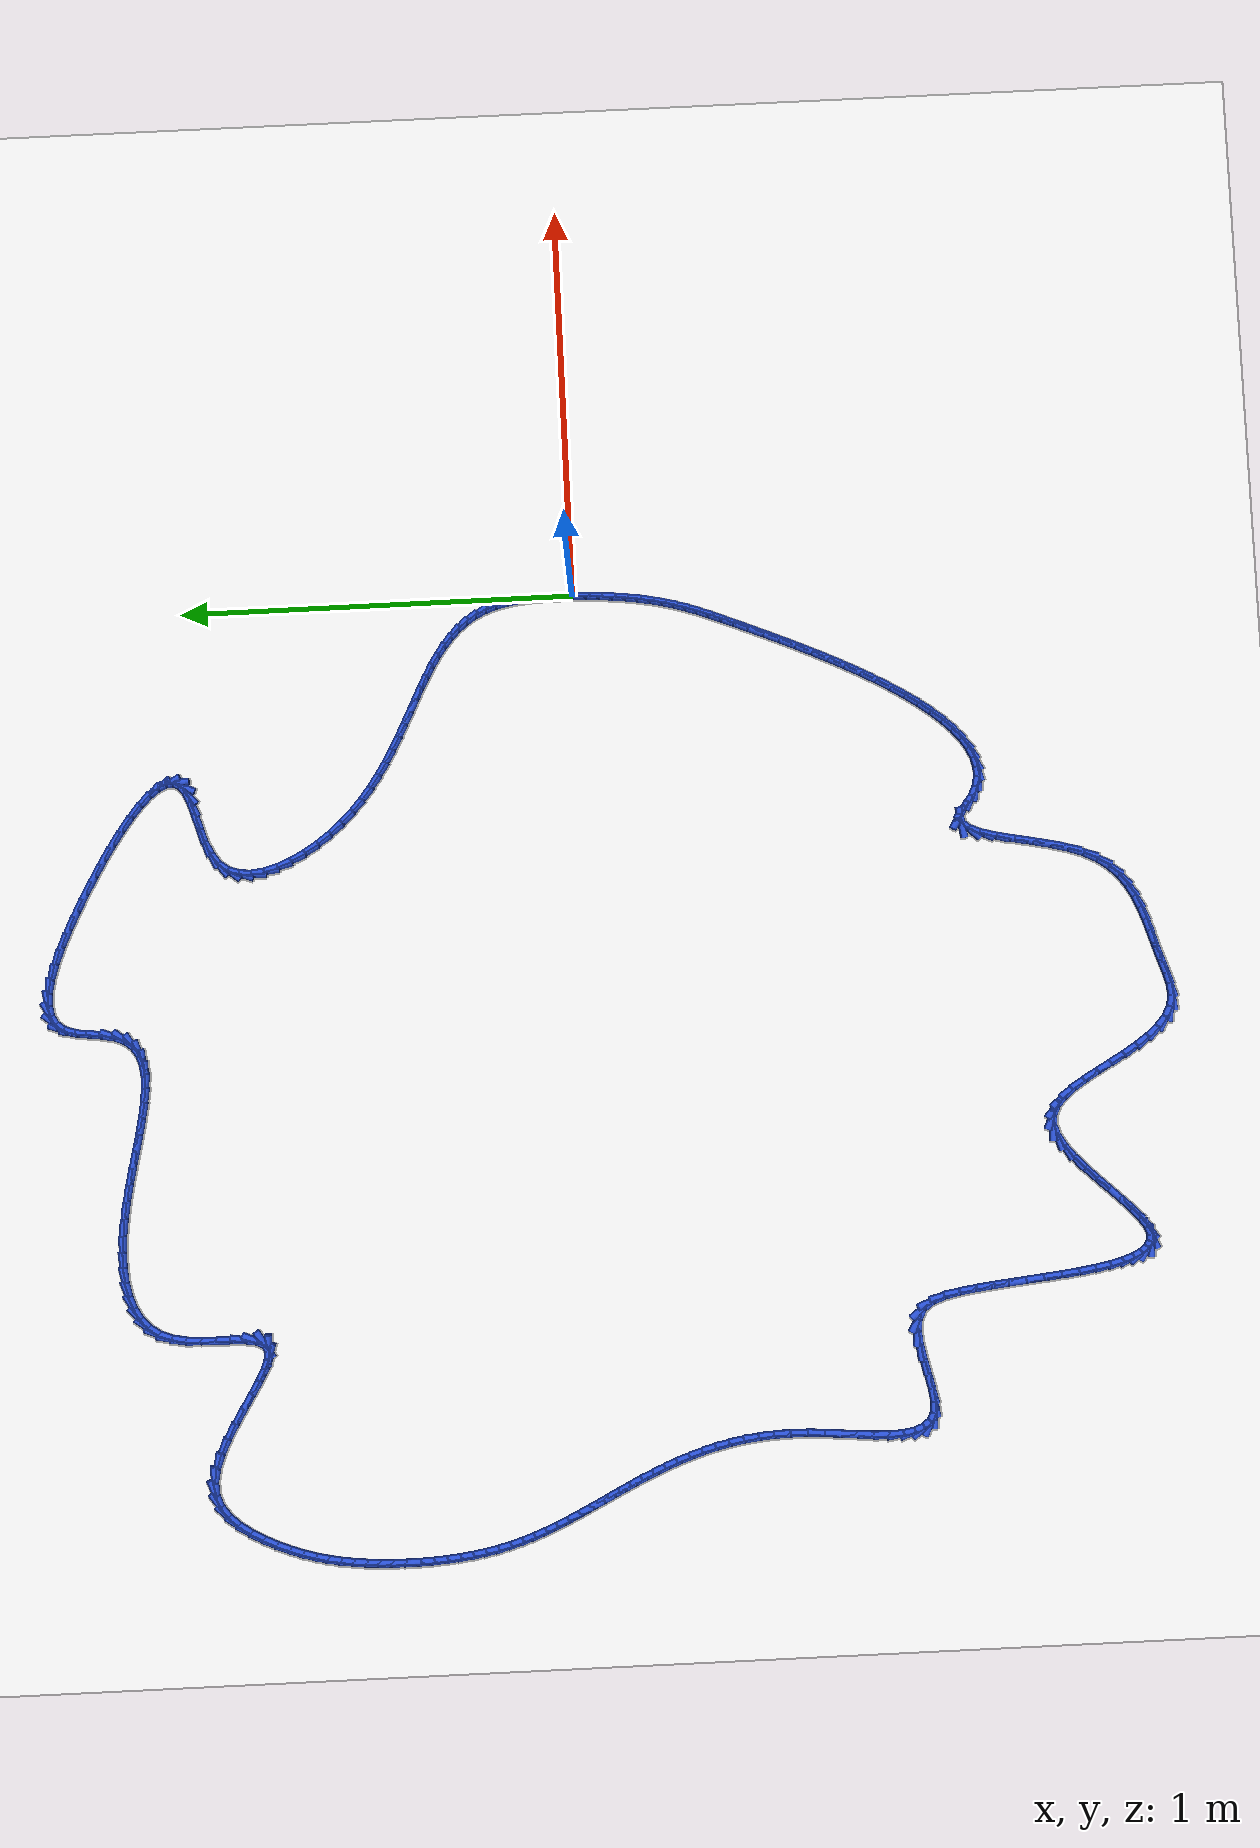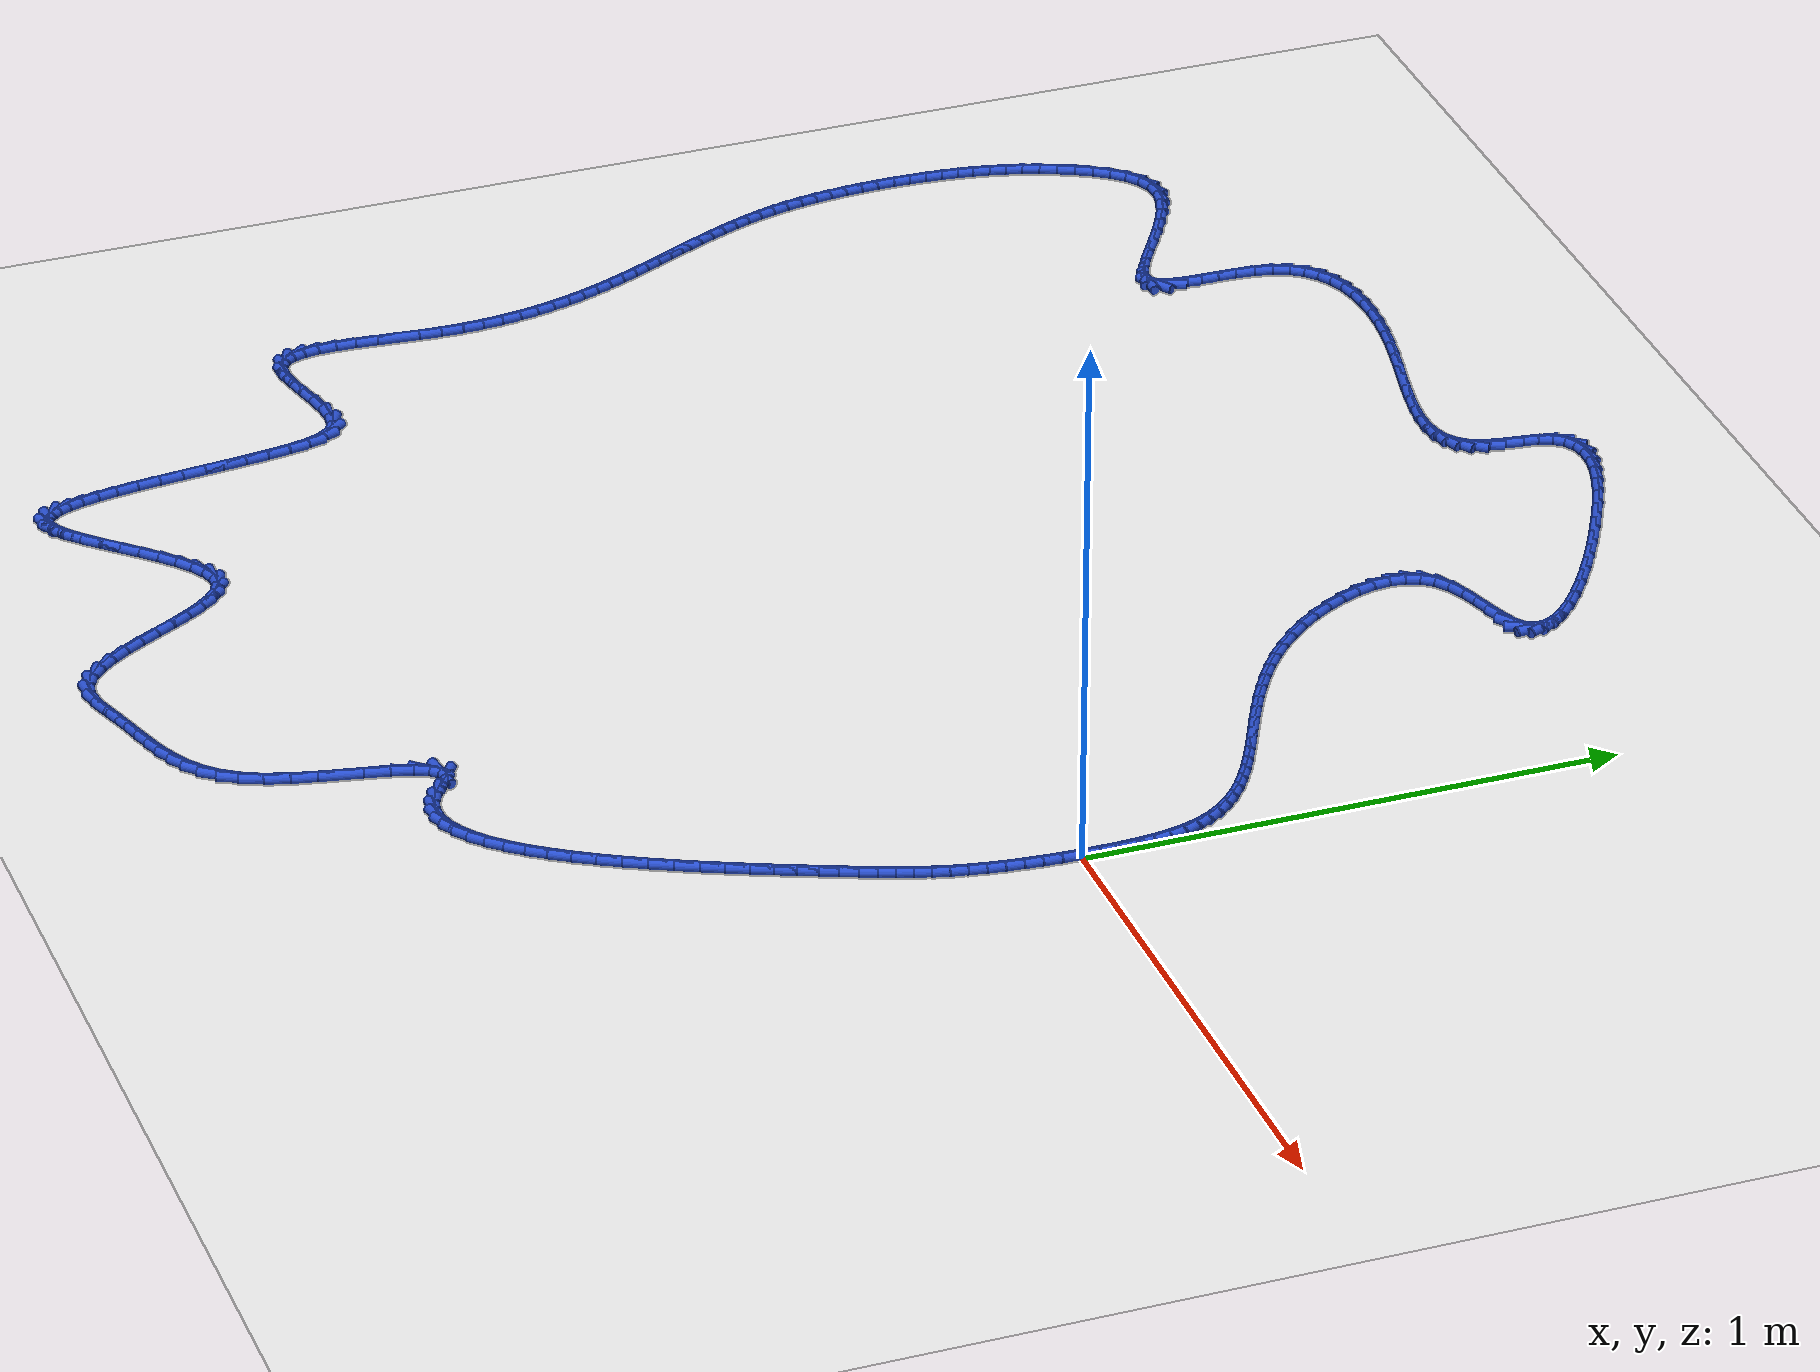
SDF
<sdf version="1.6">
 <world name="default">
  <light name="sun" type="directional">
   <pose>0 0 10 0 -0 0</pose>
   <diffuse>0.8 0.8 0.8 1</diffuse>
   <specular>0.2 0.2 0.2 1</specular>
   <attenuation>
    <range>1000</range>
    <constant>0.9</constant>
    <linear>0.01</linear>
    <quadratic>0.001</quadratic>
   </attenuation>
   <direction>-0.5 0.1 -0.9</direction>
  </light>
  <model name="ground_plane">
   <static>1</static>
   <link name="link">
    <collision name="collision">
     <geometry><plane><normal>0 0 1</normal><size>100 100</size></plane></geometry>
     <surface><friction><ode><mu>100</mu><mu2>50</mu2></ode></friction></surface>
    </collision>
    <visual name="visual">
     <cast_shadows>0</cast_shadows>
     <geometry><plane><normal>0 0 1</normal><size>100 100</size></plane></geometry>
     <material>
      <script><uri>file://media/materials/scripts/gazebo.material</uri><name>Gazebo/WhiteGlow</name></script>
     </material>
    </visual>
   </link>
  </model>
  <gravity>0 0 -9.8</gravity>
  <magnetic_field>6e-06 2.3e-05 -4.2e-05</magnetic_field>
  <atmosphere type="adiabatic"/>
  <physics name="default_physics" default="0" type="ode">
   <max_step_size>0.001</max_step_size>
   <real_time_factor>1</real_time_factor>
   <real_time_update_rate>1000</real_time_update_rate>
  </physics>
  <scene><ambient>0.4 0.4 0.4 1</ambient><background>0.7 0.7 0.7 1</background><shadows>1</shadows></scene>
  <spherical_coordinates>
   <surface_model>EARTH_WGS84</surface_model>
   <latitude_deg>0</latitude_deg>
   <longitude_deg>0</longitude_deg>
   <elevation>0</elevation>
   <heading_deg>0</heading_deg>
  </spherical_coordinates>
  <model name="line">
   <link name="link_0">
    <pose>1.235990476633475e-17 6.938893903907228e-18 0.01 0 1.57 1.551171757758314</pose>
    <collision name="collision">
     <geometry><cylinder><radius>0.01</radius><length>0.08</length></cylinder></geometry>
    </collision>
    <visual name="visual">
     <material>
      <script><name>Gazebo/Blue</name><uri>file://media/materials/scripts/gazebo.material</uri></script>
     </material>
     <geometry><cylinder><radius>0.01</radius><length>0.08</length></cylinder></geometry>
    </visual>
   </link>
   <link name="link_1">
    <pose>0.0006745324023107896 0.034367420044899434 0.01 0 1.57 -1.5639240911768244</pose>
    <collision name="collision">
     <geometry><cylinder><radius>0.01</radius><length>0.08</length></cylinder></geometry>
    </collision>
    <visual name="visual">
     <material>
      <script><name>Gazebo/Blue</name><uri>file://media/materials/scripts/gazebo.material</uri></script>
     </material>
     <geometry><cylinder><radius>0.01</radius><length>0.08</length></cylinder></geometry>
    </visual>
   </link>
   <link name="link_2">
    <pose>0.00043832751002415384 0.06873777445891724 0.01 0 1.57 -1.5269748179078124</pose>
    <collision name="collision">
     <geometry><cylinder><radius>0.01</radius><length>0.08</length></cylinder></geometry>
    </collision>
    <visual name="visual">
     <material>
      <script><name>Gazebo/Blue</name><uri>file://media/materials/scripts/gazebo.material</uri></script>
     </material>
     <geometry><cylinder><radius>0.01</radius><length>0.08</length></cylinder></geometry>
    </visual>
   </link>
   <link name="link_3">
    <pose>-0.0010501066504835894 0.10268186532563708 0.01 0 1.57 -1.477915862114082</pose>
    <collision name="collision">
     <geometry><cylinder><radius>0.01</radius><length>0.08</length></cylinder></geometry>
    </collision>
    <visual name="visual">
     <material>
      <script><name>Gazebo/Blue</name><uri>file://media/materials/scripts/gazebo.material</uri></script>
     </material>
     <geometry><cylinder><radius>0.01</radius><length>0.08</length></cylinder></geometry>
    </visual>
   </link>
   <link name="link_4">
    <pose>-0.004132262052836136 0.13577049472864247 0.01 0 1.57 -1.4143267002373296</pose>
    <collision name="collision">
     <geometry><cylinder><radius>0.01</radius><length>0.08</length></cylinder></geometry>
    </collision>
    <visual name="visual">
     <material>
      <script><name>Gazebo/Blue</name><uri>file://media/materials/scripts/gazebo.material</uri></script>
     </material>
     <geometry><cylinder><radius>0.01</radius><length>0.08</length></cylinder></geometry>
    </visual>
   </link>
   <link name="link_5">
    <pose>-0.009149630670657185 0.1675744647515172 0.01 0 1.57 -1.3329760616321287</pose>
    <collision name="collision">
     <geometry><cylinder><radius>0.01</radius><length>0.08</length></cylinder></geometry>
    </collision>
    <visual name="visual">
     <material>
      <script><name>Gazebo/Blue</name><uri>file://media/materials/scripts/gazebo.material</uri></script>
     </material>
     <geometry><cylinder><radius>0.01</radius><length>0.08</length></cylinder></geometry>
    </visual>
   </link>
   <link name="link_6">
    <pose>-0.01644370447757043 0.19766457747784472 0.01 0 1.57 -1.2299644972680142</pose>
    <collision name="collision">
     <geometry><cylinder><radius>0.01</radius><length>0.08</length></cylinder></geometry>
    </collision>
    <visual name="visual">
     <material>
      <script><name>Gazebo/Blue</name><uri>file://media/materials/scripts/gazebo.material</uri></script>
     </material>
     <geometry><cylinder><radius>0.01</radius><length>0.08</length></cylinder></geometry>
    </visual>
   </link>
   <link name="link_7">
    <pose>-0.026355835067479575 0.22561180953779056 0.01 0 1.57 -1.1078628706561144</pose>
    <collision name="collision">
     <geometry><cylinder><radius>0.01</radius><length>0.08</length></cylinder></geometry>
    </collision>
    <visual name="visual">
     <material>
      <script><name>Gazebo/Blue</name><uri>file://media/materials/scripts/gazebo.material</uri></script>
     </material>
     <geometry><cylinder><radius>0.01</radius><length>0.08</length></cylinder></geometry>
    </visual>
   </link>
   <link name="link_8">
    <pose>-0.03909993905340194 0.2511455887987932 0.01 0 1.57 -0.9859523500956935</pose>
    <collision name="collision">
     <geometry><cylinder><radius>0.01</radius><length>0.08</length></cylinder></geometry>
    </collision>
    <visual name="visual">
     <material>
      <script><name>Gazebo/Blue</name><uri>file://media/materials/scripts/gazebo.material</uri></script>
     </material>
     <geometry><cylinder><radius>0.01</radius><length>0.08</length></cylinder></geometry>
    </visual>
   </link>
   <link name="link_9">
    <pose>-0.054527475111931935 0.27444601929339246 0.01 0 1.57 -0.8725785521571431</pose>
    <collision name="collision">
     <geometry><cylinder><radius>0.01</radius><length>0.08</length></cylinder></geometry>
    </collision>
    <visual name="visual">
     <material>
      <script><name>Gazebo/Blue</name><uri>file://media/materials/scripts/gazebo.material</uri></script>
     </material>
     <geometry><cylinder><radius>0.01</radius><length>0.08</length></cylinder></geometry>
    </visual>
   </link>
   <link name="link_10">
    <pose>-0.07242589225260787 0.2957727939619144 0.01 0 1.57 -0.7717218353284312</pose>
    <collision name="collision">
     <geometry><cylinder><radius>0.01</radius><length>0.08</length></cylinder></geometry>
    </collision>
    <visual name="visual">
     <material>
      <script><name>Gazebo/Blue</name><uri>file://media/materials/scripts/gazebo.material</uri></script>
     </material>
     <geometry><cylinder><radius>0.01</radius><length>0.08</length></cylinder></geometry>
    </visual>
   </link>
   <link name="link_11">
    <pose>-0.09258263948496796 0.31538560574468494 0.01 0 1.57 -0.6855362669745999</pose>
    <collision name="collision">
     <geometry><cylinder><radius>0.01</radius><length>0.08</length></cylinder></geometry>
    </collision>
    <visual name="visual">
     <material>
      <script><name>Gazebo/Blue</name><uri>file://media/materials/scripts/gazebo.material</uri></script>
     </material>
     <geometry><cylinder><radius>0.01</radius><length>0.08</length></cylinder></geometry>
    </visual>
   </link>
   <link name="link_12">
    <pose>-0.1147851658185505 0.3335441475820299 0.01 0 1.57 -0.6145949139323338</pose>
    <collision name="collision">
     <geometry><cylinder><radius>0.01</radius><length>0.08</length></cylinder></geometry>
    </collision>
    <visual name="visual">
     <material>
      <script><name>Gazebo/Blue</name><uri>file://media/materials/scripts/gazebo.material</uri></script>
     </material>
     <geometry><cylinder><radius>0.01</radius><length>0.08</length></cylinder></geometry>
    </visual>
   </link>
   <link name="link_13">
    <pose>-0.13882092026289375 0.3505081124142754 0.01 0 1.57 -0.5584258317124778</pose>
    <collision name="collision">
     <geometry><cylinder><radius>0.01</radius><length>0.08</length></cylinder></geometry>
    </collision>
    <visual name="visual">
     <material>
      <script><name>Gazebo/Blue</name><uri>file://media/materials/scripts/gazebo.material</uri></script>
     </material>
     <geometry><cylinder><radius>0.01</radius><length>0.08</length></cylinder></geometry>
    </visual>
   </link>
   <link name="link_14">
    <pose>-0.16447735182753587 0.36653719318174705 0.01 0 1.57 -0.5160329135707314</pose>
    <collision name="collision">
     <geometry><cylinder><radius>0.01</radius><length>0.08</length></cylinder></geometry>
    </collision>
    <visual name="visual">
     <material>
      <script><name>Gazebo/Blue</name><uri>file://media/materials/scripts/gazebo.material</uri></script>
     </material>
     <geometry><cylinder><radius>0.01</radius><length>0.08</length></cylinder></geometry>
    </visual>
   </link>
   <link name="link_15">
    <pose>-0.19154190952201533 0.3818910828247711 0.01 0 1.57 -0.48626732253995403</pose>
    <collision name="collision">
     <geometry><cylinder><radius>0.01</radius><length>0.08</length></cylinder></geometry>
    </collision>
    <visual name="visual">
     <material>
      <script><name>Gazebo/Blue</name><uri>file://media/materials/scripts/gazebo.material</uri></script>
     </material>
     <geometry><cylinder><radius>0.01</radius><length>0.08</length></cylinder></geometry>
    </visual>
   </link>
   <link name="link_16">
    <pose>-0.21980204235587023 0.3968294742836733 0.01 0 1.57 -0.46804256202097166</pose>
    <collision name="collision">
     <geometry><cylinder><radius>0.01</radius><length>0.08</length></cylinder></geometry>
    </collision>
    <visual name="visual">
     <material>
      <script><name>Gazebo/Blue</name><uri>file://media/materials/scripts/gazebo.material</uri></script>
     </material>
     <geometry><cylinder><radius>0.01</radius><length>0.08</length></cylinder></geometry>
    </visual>
   </link>
   <link name="link_17">
    <pose>-0.2490451993386389 0.4116120604987798 0.01 0 1.57 -0.46043482709330746</pose>
    <collision name="collision">
     <geometry><cylinder><radius>0.01</radius><length>0.08</length></cylinder></geometry>
    </collision>
    <visual name="visual">
     <material>
      <script><name>Gazebo/Blue</name><uri>file://media/materials/scripts/gazebo.material</uri></script>
     </material>
     <geometry><cylinder><radius>0.01</radius><length>0.08</length></cylinder></geometry>
    </visual>
   </link>
   <link name="link_18">
    <pose>-0.2790588294798596 0.4264985344104164 0.01 0 1.57 -0.462712404956665</pose>
    <collision name="collision">
     <geometry><cylinder><radius>0.01</radius><length>0.08</length></cylinder></geometry>
    </collision>
    <visual name="visual">
     <material>
      <script><name>Gazebo/Blue</name><uri>file://media/materials/scripts/gazebo.material</uri></script>
     </material>
     <geometry><cylinder><radius>0.01</radius><length>0.08</length></cylinder></geometry>
    </visual>
   </link>
   <link name="link_19">
    <pose>-0.30963038178907065 0.441748588958909 0.01 0 1.57 -0.47432488857347443</pose>
    <collision name="collision">
     <geometry><cylinder><radius>0.01</radius><length>0.08</length></cylinder></geometry>
    </collision>
    <visual name="visual">
     <material>
      <script><name>Gazebo/Blue</name><uri>file://media/materials/scripts/gazebo.material</uri></script>
     </material>
     <geometry><cylinder><radius>0.01</radius><length>0.08</length></cylinder></geometry>
    </visual>
   </link>
   <link name="link_20">
    <pose>-0.3405473052758102 0.4576219170845836 0.01 0 1.57 -0.49486973653933797</pose>
    <collision name="collision">
     <geometry><cylinder><radius>0.01</radius><length>0.08</length></cylinder></geometry>
    </collision>
    <visual name="visual">
     <material>
      <script><name>Gazebo/Blue</name><uri>file://media/materials/scripts/gazebo.material</uri></script>
     </material>
     <geometry><cylinder><radius>0.01</radius><length>0.08</length></cylinder></geometry>
    </visual>
   </link>
   <link name="link_21">
    <pose>-0.37159704894961654 0.47437821172776606 0.01 0 1.57 -0.5240444670976809</pose>
    <collision name="collision">
     <geometry><cylinder><radius>0.01</radius><length>0.08</length></cylinder></geometry>
    </collision>
    <visual name="visual">
     <material>
      <script><name>Gazebo/Blue</name><uri>file://media/materials/scripts/gazebo.material</uri></script>
     </material>
     <geometry><cylinder><radius>0.01</radius><length>0.08</length></cylinder></geometry>
    </visual>
   </link>
   <link name="link_22">
    <pose>-0.402567061820028 0.49227716582878234 0.01 0 1.57 -0.5615876416291465</pose>
    <collision name="collision">
     <geometry><cylinder><radius>0.01</radius><length>0.08</length></cylinder></geometry>
    </collision>
    <visual name="visual">
     <material>
      <script><name>Gazebo/Blue</name><uri>file://media/materials/scripts/gazebo.material</uri></script>
     </material>
     <geometry><cylinder><radius>0.01</radius><length>0.08</length></cylinder></geometry>
    </visual>
   </link>
   <link name="link_23">
    <pose>-0.4332447928965827 0.5115784723279584 0.01 0 1.57 -0.6072101114378999</pose>
    <collision name="collision">
     <geometry><cylinder><radius>0.01</radius><length>0.08</length></cylinder></geometry>
    </collision>
    <visual name="visual">
     <material>
      <script><name>Gazebo/Blue</name><uri>file://media/materials/scripts/gazebo.material</uri></script>
     </material>
     <geometry><cylinder><radius>0.01</radius><length>0.08</length></cylinder></geometry>
    </visual>
   </link>
   <link name="link_24">
    <pose>-0.46341769118881904 0.5325418241656202 0.01 0 1.57 -0.6605193197187166</pose>
    <collision name="collision">
     <geometry><cylinder><radius>0.01</radius><length>0.08</length></cylinder></geometry>
    </collision>
    <visual name="visual">
     <material>
      <script><name>Gazebo/Blue</name><uri>file://media/materials/scripts/gazebo.material</uri></script>
     </material>
     <geometry><cylinder><radius>0.01</radius><length>0.08</length></cylinder></geometry>
    </visual>
   </link>
   <link name="link_25">
    <pose>-0.4928732057062754 0.5554269142820938 0.01 0 1.57 -0.7209433856596174</pose>
    <collision name="collision">
     <geometry><cylinder><radius>0.01</radius><length>0.08</length></cylinder></geometry>
    </collision>
    <visual name="visual">
     <material>
      <script><name>Gazebo/Blue</name><uri>file://media/materials/scripts/gazebo.material</uri></script>
     </material>
     <geometry><cylinder><radius>0.01</radius><length>0.08</length></cylinder></geometry>
    </visual>
   </link>
   <link name="link_26">
    <pose>-0.5213987854584898 0.580493435617705 0.01 0 1.57 -0.7876672398565674</pose>
    <collision name="collision">
     <geometry><cylinder><radius>0.01</radius><length>0.08</length></cylinder></geometry>
    </collision>
    <visual name="visual">
     <material>
      <script><name>Gazebo/Blue</name><uri>file://media/materials/scripts/gazebo.material</uri></script>
     </material>
     <geometry><cylinder><radius>0.01</radius><length>0.08</length></cylinder></geometry>
    </visual>
   </link>
   <link name="link_27">
    <pose>-0.5487818794550003 0.6080010811127793 0.01 0 1.57 -0.8595334222569369</pose>
    <collision name="collision">
     <geometry><cylinder><radius>0.01</radius><length>0.08</length></cylinder></geometry>
    </collision>
    <visual name="visual">
     <material>
      <script><name>Gazebo/Blue</name><uri>file://media/materials/scripts/gazebo.material</uri></script>
     </material>
     <geometry><cylinder><radius>0.01</radius><length>0.08</length></cylinder></geometry>
    </visual>
   </link>
   <link name="link_28">
    <pose>-0.5748051520950431 0.6382000574813455 0.01 0 1.57 -0.9332393618627947</pose>
    <collision name="collision">
     <geometry><cylinder><radius>0.01</radius><length>0.08</length></cylinder></geometry>
    </collision>
    <visual name="visual">
     <material>
      <script><name>Gazebo/Blue</name><uri>file://media/materials/scripts/gazebo.material</uri></script>
     </material>
     <geometry><cylinder><radius>0.01</radius><length>0.08</length></cylinder></geometry>
    </visual>
   </link>
   <link name="link_29">
    <pose>-0.5990318488802844 0.670905539703456 0.01 0 1.57 -1.0085580655554982</pose>
    <collision name="collision">
     <geometry><cylinder><radius>0.01</radius><length>0.08</length></cylinder></geometry>
    </collision>
    <visual name="visual">
     <material>
      <script><name>Gazebo/Blue</name><uri>file://media/materials/scripts/gazebo.material</uri></script>
     </material>
     <geometry><cylinder><radius>0.01</radius><length>0.08</length></cylinder></geometry>
    </visual>
   </link>
   <link name="link_30">
    <pose>-0.6207191855864936 0.7053259517282369 0.01 0 1.57 -1.0906720595886172</pose>
    <collision name="collision">
     <geometry><cylinder><radius>0.01</radius><length>0.08</length></cylinder></geometry>
    </collision>
    <visual name="visual">
     <material>
      <script><name>Gazebo/Blue</name><uri>file://media/materials/scripts/gazebo.material</uri></script>
     </material>
     <geometry><cylinder><radius>0.01</radius><length>0.08</length></cylinder></geometry>
    </visual>
   </link>
   <link name="link_31">
    <pose>-0.6391016679178374 0.7406246912926802 0.01 0 1.57 -1.186005393886624</pose>
    <collision name="collision">
     <geometry><cylinder><radius>0.01</radius><length>0.08</length></cylinder></geometry>
    </collision>
    <visual name="visual">
     <material>
      <script><name>Gazebo/Blue</name><uri>file://media/materials/scripts/gazebo.material</uri></script>
     </material>
     <geometry><cylinder><radius>0.01</radius><length>0.08</length></cylinder></geometry>
    </visual>
   </link>
   <link name="link_32">
    <pose>-0.6534138015784827 0.7759651561337785 0.01 0 1.57 -1.3030692803742807</pose>
    <collision name="collision">
     <geometry><cylinder><radius>0.01</radius><length>0.08</length></cylinder></geometry>
    </collision>
    <visual name="visual">
     <material>
      <script><name>Gazebo/Blue</name><uri>file://media/materials/scripts/gazebo.material</uri></script>
     </material>
     <geometry><cylinder><radius>0.01</radius><length>0.08</length></cylinder></geometry>
    </visual>
   </link>
   <link name="link_33">
    <pose>-0.6628900922725963 0.8105107439885243 0.01 0 1.57 -1.4536065105559255</pose>
    <collision name="collision">
     <geometry><cylinder><radius>0.01</radius><length>0.08</length></cylinder></geometry>
    </collision>
    <visual name="visual">
     <material>
      <script><name>Gazebo/Blue</name><uri>file://media/materials/scripts/gazebo.material</uri></script>
     </material>
     <geometry><cylinder><radius>0.01</radius><length>0.08</length></cylinder></geometry>
    </visual>
   </link>
   <link name="link_34">
    <pose>-0.6667650457043451 0.8434248525939102 0.01 0 1.57 1.4891325931933959</pose>
    <collision name="collision">
     <geometry><cylinder><radius>0.01</radius><length>0.08</length></cylinder></geometry>
    </collision>
    <visual name="visual">
     <material>
      <script><name>Gazebo/Blue</name><uri>file://media/materials/scripts/gazebo.material</uri></script>
     </material>
     <geometry><cylinder><radius>0.01</radius><length>0.08</length></cylinder></geometry>
    </visual>
   </link>
   <link name="link_35">
    <pose>-0.6642731675778962 0.8738708796869287 0.01 0 1.57 1.2300332123612554</pose>
    <collision name="collision">
     <geometry><cylinder><radius>0.01</radius><length>0.08</length></cylinder></geometry>
    </collision>
    <visual name="visual">
     <material>
      <script><name>Gazebo/Blue</name><uri>file://media/materials/scripts/gazebo.material</uri></script>
     </material>
     <geometry><cylinder><radius>0.01</radius><length>0.08</length></cylinder></geometry>
    </visual>
   </link>
   <link name="link_36">
    <pose>-0.6546489635974158 0.9010122230045716 0.01 0 1.57 0.9197699224399859</pose>
    <collision name="collision">
     <geometry><cylinder><radius>0.01</radius><length>0.08</length></cylinder></geometry>
    </collision>
    <visual name="visual">
     <material>
      <script><name>Gazebo/Blue</name><uri>file://media/materials/scripts/gazebo.material</uri></script>
     </material>
     <geometry><cylinder><radius>0.01</radius><length>0.08</length></cylinder></geometry>
    </visual>
   </link>
   <link name="link_37">
    <pose>-0.6371269394670711 0.9240122802838328 0.01 0 1.57 0.6194473717503187</pose>
    <collision name="collision">
     <geometry><cylinder><radius>0.01</radius><length>0.08</length></cylinder></geometry>
    </collision>
    <visual name="visual">
     <material>
      <script><name>Gazebo/Blue</name><uri>file://media/materials/scripts/gazebo.material</uri></script>
     </material>
     <geometry><cylinder><radius>0.01</radius><length>0.08</length></cylinder></geometry>
    </visual>
   </link>
   <link name="link_38">
    <pose>-0.6114537484375069 0.9423191922987368 0.01 0 1.57 0.42852501772104457</pose>
    <collision name="collision">
     <geometry><cylinder><radius>0.01</radius><length>0.08</length></cylinder></geometry>
    </collision>
    <visual name="visual">
     <material>
      <script><name>Gazebo/Blue</name><uri>file://media/materials/scripts/gazebo.material</uri></script>
     </material>
     <geometry><cylinder><radius>0.01</radius><length>0.08</length></cylinder></geometry>
    </visual>
   </link>
   <link name="link_39">
    <pose>-0.5798503829352134 0.9567567792665215 0.01 0 1.57 0.32914970800333143</pose>
    <collision name="collision">
     <geometry><cylinder><radius>0.01</radius><length>0.08</length></cylinder></geometry>
    </collision>
    <visual name="visual">
     <material>
      <script><name>Gazebo/Blue</name><uri>file://media/materials/scripts/gazebo.material</uri></script>
     </material>
     <geometry><cylinder><radius>0.01</radius><length>0.08</length></cylinder></geometry>
    </visual>
   </link>
   <link name="link_40">
    <pose>-0.5452840911622212 0.9685637635891405 0.01 0 1.57 0.2926945093638431</pose>
    <collision name="collision">
     <geometry><cylinder><radius>0.01</radius><length>0.08</length></cylinder></geometry>
    </collision>
    <visual name="visual">
     <material>
      <script><name>Gazebo/Blue</name><uri>file://media/materials/scripts/gazebo.material</uri></script>
     </material>
     <geometry><cylinder><radius>0.01</radius><length>0.08</length></cylinder></geometry>
    </visual>
   </link>
   <link name="link_41">
    <pose>-0.5107222753914705 0.9789789533286649 0.01 0 1.57 0.31410229428454683</pose>
    <collision name="collision">
     <geometry><cylinder><radius>0.01</radius><length>0.08</length></cylinder></geometry>
    </collision>
    <visual name="visual">
     <material>
      <script><name>Gazebo/Blue</name><uri>file://media/materials/scripts/gazebo.material</uri></script>
     </material>
     <geometry><cylinder><radius>0.01</radius><length>0.08</length></cylinder></geometry>
    </visual>
   </link>
   <link name="link_42">
    <pose>-0.4791323378959036 0.9892411565471664 0.01 0 1.57 0.4165214956059197</pose>
    <collision name="collision">
     <geometry><cylinder><radius>0.01</radius><length>0.08</length></cylinder></geometry>
    </collision>
    <visual name="visual">
     <material>
      <script><name>Gazebo/Blue</name><uri>file://media/materials/scripts/gazebo.material</uri></script>
     </material>
     <geometry><cylinder><radius>0.01</radius><length>0.08</length></cylinder></geometry>
    </visual>
   </link>
   <link name="link_43">
    <pose>-0.45348168094846103 1.0005891813067163 0.01 0 1.57 0.6797086663926685</pose>
    <collision name="collision">
     <geometry><cylinder><radius>0.01</radius><length>0.08</length></cylinder></geometry>
    </collision>
    <visual name="visual">
     <material>
      <script><name>Gazebo/Blue</name><uri>file://media/materials/scripts/gazebo.material</uri></script>
     </material>
     <geometry><cylinder><radius>0.01</radius><length>0.08</length></cylinder></geometry>
    </visual>
   </link>
   <link name="link_44">
    <pose>-0.43662278552695 1.0142141973778662 0.01 0 1.57 1.1543749748583172</pose>
    <collision name="collision">
     <geometry><cylinder><radius>0.01</radius><length>0.08</length></cylinder></geometry>
    </collision>
    <visual name="visual">
     <material>
      <script><name>Gazebo/Blue</name><uri>file://media/materials/scripts/gazebo.material</uri></script>
     </material>
     <geometry><cylinder><radius>0.01</radius><length>0.08</length></cylinder></geometry>
    </visual>
   </link>
   <link name="link_45">
    <pose>-0.4294260853999631 1.0304857570698576 0.01 0 1.57 -1.481563053469985</pose>
    <collision name="collision">
     <geometry><cylinder><radius>0.01</radius><length>0.08</length></cylinder></geometry>
    </collision>
    <visual name="visual">
     <material>
      <script><name>Gazebo/Blue</name><uri>file://media/materials/scripts/gazebo.material</uri></script>
     </material>
     <geometry><cylinder><radius>0.01</radius><length>0.08</length></cylinder></geometry>
    </visual>
   </link>
   <link name="link_46">
    <pose>-0.431089747169748 1.0490802082629678 0.01 0 1.57 -1.1313971508245861</pose>
    <collision name="collision">
     <geometry><cylinder><radius>0.01</radius><length>0.08</length></cylinder></geometry>
    </collision>
    <visual name="visual">
     <material>
      <script><name>Gazebo/Blue</name><uri>file://media/materials/scripts/gazebo.material</uri></script>
     </material>
     <geometry><cylinder><radius>0.01</radius><length>0.08</length></cylinder></geometry>
    </visual>
   </link>
   <link name="link_47">
    <pose>-0.440759533652331 1.069652175910996 0.01 0 1.57 -0.9224534851953125</pose>
    <collision name="collision">
     <geometry><cylinder><radius>0.01</radius><length>0.08</length></cylinder></geometry>
    </collision>
    <visual name="visual">
     <material>
      <script><name>Gazebo/Blue</name><uri>file://media/materials/scripts/gazebo.material</uri></script>
     </material>
     <geometry><cylinder><radius>0.01</radius><length>0.08</length></cylinder></geometry>
    </visual>
   </link>
   <link name="link_48">
    <pose>-0.45758120766373794 1.091856284967744 0.01 0 1.57 -0.7933694485484077</pose>
    <collision name="collision">
     <geometry><cylinder><radius>0.01</radius><length>0.08</length></cylinder></geometry>
    </collision>
    <visual name="visual">
     <material>
      <script><name>Gazebo/Blue</name><uri>file://media/materials/scripts/gazebo.material</uri></script>
     </material>
     <geometry><cylinder><radius>0.01</radius><length>0.08</length></cylinder></geometry>
    </visual>
   </link>
   <link name="link_49">
    <pose>-0.4807005320199945 1.115347160387011 0.01 0 1.57 -0.7076146568592331</pose>
    <collision name="collision">
     <geometry><cylinder><radius>0.01</radius><length>0.08</length></cylinder></geometry>
    </collision>
    <visual name="visual">
     <material>
      <script><name>Gazebo/Blue</name><uri>file://media/materials/scripts/gazebo.material</uri></script>
     </material>
     <geometry><cylinder><radius>0.01</radius><length>0.08</length></cylinder></geometry>
    </visual>
   </link>
   <link name="link_50">
    <pose>-0.509263269537127 1.1397794271225987 0.01 0 1.57 -0.646666313776083</pose>
    <collision name="collision">
     <geometry><cylinder><radius>0.01</radius><length>0.08</length></cylinder></geometry>
    </collision>
    <visual name="visual">
     <material>
      <script><name>Gazebo/Blue</name><uri>file://media/materials/scripts/gazebo.material</uri></script>
     </material>
     <geometry><cylinder><radius>0.01</radius><length>0.08</length></cylinder></geometry>
    </visual>
   </link>
   <link name="link_51">
    <pose>-0.5424151830311605 1.1648077101283063 0.01 0 1.57 -0.6007986333091562</pose>
    <collision name="collision">
     <geometry><cylinder><radius>0.01</radius><length>0.08</length></cylinder></geometry>
    </collision>
    <visual name="visual">
     <material>
      <script><name>Gazebo/Blue</name><uri>file://media/materials/scripts/gazebo.material</uri></script>
     </material>
     <geometry><cylinder><radius>0.01</radius><length>0.08</length></cylinder></geometry>
    </visual>
   </link>
   <link name="link_52">
    <pose>-0.5793020353181219 1.190086634357935 0.01 0 1.57 -0.5645348074314845</pose>
    <collision name="collision">
     <geometry><cylinder><radius>0.01</radius><length>0.08</length></cylinder></geometry>
    </collision>
    <visual name="visual">
     <material>
      <script><name>Gazebo/Blue</name><uri>file://media/materials/scripts/gazebo.material</uri></script>
     </material>
     <geometry><cylinder><radius>0.01</radius><length>0.08</length></cylinder></geometry>
    </visual>
   </link>
   <link name="link_53">
    <pose>-0.619069589214036 1.2152708247652846 0.01 0 1.57 -0.5345522174541816</pose>
    <collision name="collision">
     <geometry><cylinder><radius>0.01</radius><length>0.08</length></cylinder></geometry>
    </collision>
    <visual name="visual">
     <material>
      <script><name>Gazebo/Blue</name><uri>file://media/materials/scripts/gazebo.material</uri></script>
     </material>
     <geometry><cylinder><radius>0.01</radius><length>0.08</length></cylinder></geometry>
    </visual>
   </link>
   <link name="link_54">
    <pose>-0.6608636075349292 1.2400149063041555 0.01 0 1.57 -0.5086704039617261</pose>
    <collision name="collision">
     <geometry><cylinder><radius>0.01</radius><length>0.08</length></cylinder></geometry>
    </collision>
    <visual name="visual">
     <material>
      <script><name>Gazebo/Blue</name><uri>file://media/materials/scripts/gazebo.material</uri></script>
     </material>
     <geometry><cylinder><radius>0.01</radius><length>0.08</length></cylinder></geometry>
    </visual>
   </link>
   <link name="link_55">
    <pose>-0.7038298530968277 1.2639735039283484 0.01 0 1.57 -0.4852911438079115</pose>
    <collision name="collision">
     <geometry><cylinder><radius>0.01</radius><length>0.08</length></cylinder></geometry>
    </collision>
    <visual name="visual">
     <material>
      <script><name>Gazebo/Blue</name><uri>file://media/materials/scripts/gazebo.material</uri></script>
     </material>
     <geometry><cylinder><radius>0.01</radius><length>0.08</length></cylinder></geometry>
    </visual>
   </link>
   <link name="link_56">
    <pose>-0.7471146786405525 1.2867999608270342 0.01 0 1.57 -0.45991084315033526</pose>
    <collision name="collision">
     <geometry><cylinder><radius>0.01</radius><length>0.08</length></cylinder></geometry>
    </collision>
    <visual name="visual">
     <material>
      <script><name>Gazebo/Blue</name><uri>file://media/materials/scripts/gazebo.material</uri></script>
     </material>
     <geometry><cylinder><radius>0.01</radius><length>0.08</length></cylinder></geometry>
    </visual>
   </link>
   <link name="link_57">
    <pose>-0.7899289364574092 1.3080074781865307 0.01 0 1.57 -0.42450833262558463</pose>
    <collision name="collision">
     <geometry><cylinder><radius>0.01</radius><length>0.08</length></cylinder></geometry>
    </collision>
    <visual name="visual">
     <material>
      <script><name>Gazebo/Blue</name><uri>file://media/materials/scripts/gazebo.material</uri></script>
     </material>
     <geometry><cylinder><radius>0.01</radius><length>0.08</length></cylinder></geometry>
    </visual>
   </link>
   <link name="link_58">
    <pose>-0.8316052061031922 1.326844773138308 0.01 0 1.57 -0.3747156449709519</pose>
    <collision name="collision">
     <geometry><cylinder><radius>0.01</radius><length>0.08</length></cylinder></geometry>
    </collision>
    <visual name="visual">
     <material>
      <script><name>Gazebo/Blue</name><uri>file://media/materials/scripts/gazebo.material</uri></script>
     </material>
     <geometry><cylinder><radius>0.01</radius><length>0.08</length></cylinder></geometry>
    </visual>
   </link>
   <link name="link_59">
    <pose>-0.8714895710528862 1.342531222046853 0.01 0 1.57 -0.30423324147970765</pose>
    <collision name="collision">
     <geometry><cylinder><radius>0.01</radius><length>0.08</length></cylinder></geometry>
    </collision>
    <visual name="visual">
     <material>
      <script><name>Gazebo/Blue</name><uri>file://media/materials/scripts/gazebo.material</uri></script>
     </material>
     <geometry><cylinder><radius>0.01</radius><length>0.08</length></cylinder></geometry>
    </visual>
   </link>
   <link name="link_60">
    <pose>-0.9089281147814735 1.354286201276651 0.01 0 1.57 -0.2022944727932691</pose>
    <collision name="collision">
     <geometry><cylinder><radius>0.01</radius><length>0.08</length></cylinder></geometry>
    </collision>
    <visual name="visual">
     <material>
      <script><name>Gazebo/Blue</name><uri>file://media/materials/scripts/gazebo.material</uri></script>
     </material>
     <geometry><cylinder><radius>0.01</radius><length>0.08</length></cylinder></geometry>
    </visual>
   </link>
   <link name="link_61">
    <pose>-0.943266920763938 1.361329087192188 0.01 0 1.57 -0.050640377547561725</pose>
    <collision name="collision">
     <geometry><cylinder><radius>0.01</radius><length>0.08</length></cylinder></geometry>
    </collision>
    <visual name="visual">
     <material>
      <script><name>Gazebo/Blue</name><uri>file://media/materials/scripts/gazebo.material</uri></script>
     </material>
     <geometry><cylinder><radius>0.01</radius><length>0.08</length></cylinder></geometry>
    </visual>
   </link>
   <link name="link_62">
    <pose>-0.9738520724752634 1.3628792561579501 0.01 0 1.57 0.17850758811531217</pose>
    <collision name="collision">
     <geometry><cylinder><radius>0.01</radius><length>0.08</length></cylinder></geometry>
    </collision>
    <visual name="visual">
     <material>
      <script><name>Gazebo/Blue</name><uri>file://media/materials/scripts/gazebo.material</uri></script>
     </material>
     <geometry><cylinder><radius>0.01</radius><length>0.08</length></cylinder></geometry>
    </visual>
   </link>
   <link name="link_63">
    <pose>-1.0000296533904327 1.3581560845384228 0.01 0 1.57 0.5087606316774902</pose>
    <collision name="collision">
     <geometry><cylinder><radius>0.01</radius><length>0.08</length></cylinder></geometry>
    </collision>
    <visual name="visual">
     <material>
      <script><name>Gazebo/Blue</name><uri>file://media/materials/scripts/gazebo.material</uri></script>
     </material>
     <geometry><cylinder><radius>0.01</radius><length>0.08</length></cylinder></geometry>
    </visual>
   </link>
   <link name="link_64">
    <pose>-1.0211457469844292 1.3463789486980922 0.01 0 1.57 0.9050958096649662</pose>
    <collision name="collision">
     <geometry><cylinder><radius>0.01</radius><length>0.08</length></cylinder></geometry>
    </collision>
    <visual name="visual">
     <material>
      <script><name>Gazebo/Blue</name><uri>file://media/materials/scripts/gazebo.material</uri></script>
     </material>
     <geometry><cylinder><radius>0.01</radius><length>0.08</length></cylinder></geometry>
    </visual>
   </link>
   <link name="link_65">
    <pose>-1.0365464367322366 1.3267672250014442 0.01 0 1.57 1.2427885400682162</pose>
    <collision name="collision">
     <geometry><cylinder><radius>0.01</radius><length>0.08</length></cylinder></geometry>
    </collision>
    <visual name="visual">
     <material>
      <script><name>Gazebo/Blue</name><uri>file://media/materials/scripts/gazebo.material</uri></script>
     </material>
     <geometry><cylinder><radius>0.01</radius><length>0.08</length></cylinder></geometry>
    </visual>
   </link>
   <link name="link_66">
    <pose>-1.0459744554604402 1.2990622392750586 0.01 0 1.57 1.405952866264438</pose>
    <collision name="collision">
     <geometry><cylinder><radius>0.01</radius><length>0.08</length></cylinder></geometry>
    </collision>
    <visual name="visual">
     <material>
      <script><name>Gazebo/Blue</name><uri>file://media/materials/scripts/gazebo.material</uri></script>
     </material>
     <geometry><cylinder><radius>0.01</radius><length>0.08</length></cylinder></geometry>
    </visual>
   </link>
   <link name="link_67">
    <pose>-1.0514697618258753 1.2660282285933602 0.01 0 1.57 1.4432055809954663</pose>
    <collision name="collision">
     <geometry><cylinder><radius>0.01</radius><length>0.08</length></cylinder></geometry>
    </collision>
    <visual name="visual">
     <material>
      <script><name>Gazebo/Blue</name><uri>file://media/materials/scripts/gazebo.material</uri></script>
     </material>
     <geometry><cylinder><radius>0.01</radius><length>0.08</length></cylinder></geometry>
    </visual>
   </link>
   <link name="link_68">
    <pose>-1.0558973680863801 1.2315151151113182 0.01 0 1.57 1.3794566383342595</pose>
    <collision name="collision">
     <geometry><cylinder><radius>0.01</radius><length>0.08</length></cylinder></geometry>
    </collision>
    <visual name="visual">
     <material>
      <script><name>Gazebo/Blue</name><uri>file://media/materials/scripts/gazebo.material</uri></script>
     </material>
     <geometry><cylinder><radius>0.01</radius><length>0.08</length></cylinder></geometry>
    </visual>
   </link>
   <link name="link_69">
    <pose>-1.062123360088504 1.1993742337154465 0.01 0 1.57 1.1851676236772388</pose>
    <collision name="collision">
     <geometry><cylinder><radius>0.01</radius><length>0.08</length></cylinder></geometry>
    </collision>
    <visual name="visual">
     <material>
      <script><name>Gazebo/Blue</name><uri>file://media/materials/scripts/gazebo.material</uri></script>
     </material>
     <geometry><cylinder><radius>0.01</radius><length>0.08</length></cylinder></geometry>
    </visual>
   </link>
   <link name="link_70">
    <pose>-1.072776808039308 1.1731312504772082 0.01 0 1.57 0.895990376325215</pose>
    <collision name="collision">
     <geometry><cylinder><radius>0.01</radius><length>0.08</length></cylinder></geometry>
    </collision>
    <visual name="visual">
     <material>
      <script><name>Gazebo/Blue</name><uri>file://media/materials/scripts/gazebo.material</uri></script>
     </material>
     <geometry><cylinder><radius>0.01</radius><length>0.08</length></cylinder></geometry>
    </visual>
   </link>
   <link name="link_71">
    <pose>-1.0884611127939792 1.1535284820700087 0.01 0 1.57 0.5915606954719248</pose>
    <collision name="collision">
     <geometry><cylinder><radius>0.01</radius><length>0.08</length></cylinder></geometry>
    </collision>
    <visual name="visual">
     <material>
      <script><name>Gazebo/Blue</name><uri>file://media/materials/scripts/gazebo.material</uri></script>
     </material>
     <geometry><cylinder><radius>0.01</radius><length>0.08</length></cylinder></geometry>
    </visual>
   </link>
   <link name="link_72">
    <pose>-1.1087522503657459 1.1398965230059936 0.01 0 1.57 0.3285878636843313</pose>
    <collision name="collision">
     <geometry><cylinder><radius>0.01</radius><length>0.08</length></cylinder></geometry>
    </collision>
    <visual name="visual">
     <material>
      <script><name>Gazebo/Blue</name><uri>file://media/materials/scripts/gazebo.material</uri></script>
     </material>
     <geometry><cylinder><radius>0.01</radius><length>0.08</length></cylinder></geometry>
    </visual>
   </link>
   <link name="link_73">
    <pose>-1.133218159752425 1.131554924621882 0.01 0 1.57 0.131525168505087</pose>
    <collision name="collision">
     <geometry><cylinder><radius>0.01</radius><length>0.08</length></cylinder></geometry>
    </collision>
    <visual name="visual">
     <material>
      <script><name>Gazebo/Blue</name><uri>file://media/materials/scripts/gazebo.material</uri></script>
     </material>
     <geometry><cylinder><radius>0.01</radius><length>0.08</length></cylinder></geometry>
    </visual>
   </link>
   <link name="link_74">
    <pose>-1.161426779951832 1.1278232382543925 0.01 0 1.57 -0.006274713537314527</pose>
    <collision name="collision">
     <geometry><cylinder><radius>0.01</radius><length>0.08</length></cylinder></geometry>
    </collision>
    <visual name="visual">
     <material>
      <script><name>Gazebo/Blue</name><uri>file://media/materials/scripts/gazebo.material</uri></script>
     </material>
     <geometry><cylinder><radius>0.01</radius><length>0.08</length></cylinder></geometry>
    </visual>
   </link>
   <link name="link_75">
    <pose>-1.1929460499617828 1.1280210152402441 0.01 0 1.57 -0.09987030137437107</pose>
    <collision name="collision">
     <geometry><cylinder><radius>0.01</radius><length>0.08</length></cylinder></geometry>
    </collision>
    <visual name="visual">
     <material>
      <script><name>Gazebo/Blue</name><uri>file://media/materials/scripts/gazebo.material</uri></script>
     </material>
     <geometry><cylinder><radius>0.01</radius><length>0.08</length></cylinder></geometry>
    </visual>
   </link>
   <link name="link_76">
    <pose>-1.2273439087800928 1.1314678069161548 0.01 0 1.57 -0.1618360470640728</pose>
    <collision name="collision">
     <geometry><cylinder><radius>0.01</radius><length>0.08</length></cylinder></geometry>
    </collision>
    <visual name="visual">
     <material>
      <script><name>Gazebo/Blue</name><uri>file://media/materials/scripts/gazebo.material</uri></script>
     </material>
     <geometry><cylinder><radius>0.01</radius><length>0.08</length></cylinder></geometry>
    </visual>
   </link>
   <link name="link_77">
    <pose>-1.2641882954045789 1.137483164618844 0.01 0 1.57 -0.2006523695797265</pose>
    <collision name="collision">
     <geometry><cylinder><radius>0.01</radius><length>0.08</length></cylinder></geometry>
    </collision>
    <visual name="visual">
     <material>
      <script><name>Gazebo/Blue</name><uri>file://media/materials/scripts/gazebo.material</uri></script>
     </material>
     <geometry><cylinder><radius>0.01</radius><length>0.08</length></cylinder></geometry>
    </visual>
   </link>
   <link name="link_78">
    <pose>-1.303047148833057 1.1453866396850299 0.01 0 1.57 -0.22159356886565013</pose>
    <collision name="collision">
     <geometry><cylinder><radius>0.01</radius><length>0.08</length></cylinder></geometry>
    </collision>
    <visual name="visual">
     <material>
      <script><name>Gazebo/Blue</name><uri>file://media/materials/scripts/gazebo.material</uri></script>
     </material>
     <geometry><cylinder><radius>0.01</radius><length>0.08</length></cylinder></geometry>
    </visual>
   </link>
   <link name="link_79">
    <pose>-1.3434884080633427 1.1544977834514314 0.01 0 1.57 -0.2277186369212504</pose>
    <collision name="collision">
     <geometry><cylinder><radius>0.01</radius><length>0.08</length></cylinder></geometry>
    </collision>
    <visual name="visual">
     <material>
      <script><name>Gazebo/Blue</name><uri>file://media/materials/scripts/gazebo.material</uri></script>
     </material>
     <geometry><cylinder><radius>0.01</radius><length>0.08</length></cylinder></geometry>
    </visual>
   </link>
   <link name="link_80">
    <pose>-1.3850800120932516 1.164136147254767 0.01 0 1.57 -0.22053616983571817</pose>
    <collision name="collision">
     <geometry><cylinder><radius>0.01</radius><length>0.08</length></cylinder></geometry>
    </collision>
    <visual name="visual">
     <material>
      <script><name>Gazebo/Blue</name><uri>file://media/materials/scripts/gazebo.material</uri></script>
     </material>
     <geometry><cylinder><radius>0.01</radius><length>0.08</length></cylinder></geometry>
    </visual>
   </link>
   <link name="link_81">
    <pose>-1.4273898999206 1.173621282431756 0.01 0 1.57 -0.2003787789697362</pose>
    <collision name="collision">
     <geometry><cylinder><radius>0.01</radius><length>0.08</length></cylinder></geometry>
    </collision>
    <visual name="visual">
     <material>
      <script><name>Gazebo/Blue</name><uri>file://media/materials/scripts/gazebo.material</uri></script>
     </material>
     <geometry><cylinder><radius>0.01</radius><length>0.08</length></cylinder></geometry>
    </visual>
   </link>
   <link name="link_82">
    <pose>-1.4699860105432045 1.1822727403191164 0.01 0 1.57 -0.16657673213014057</pose>
    <collision name="collision">
     <geometry><cylinder><radius>0.01</radius><length>0.08</length></cylinder></geometry>
    </collision>
    <visual name="visual">
     <material>
      <script><name>Gazebo/Blue</name><uri>file://media/materials/scripts/gazebo.material</uri></script>
     </material>
     <geometry><cylinder><radius>0.01</radius><length>0.08</length></cylinder></geometry>
    </visual>
   </link>
   <link name="link_83">
    <pose>-1.5124362718185183 1.1894101039607892 0.01 0 1.57 -0.11916077345939476</pose>
    <collision name="collision">
     <geometry><cylinder><radius>0.01</radius><length>0.08</length></cylinder></geometry>
    </collision>
    <visual name="visual">
     <material>
      <script><name>Gazebo/Blue</name><uri>file://media/materials/scripts/gazebo.material</uri></script>
     </material>
     <geometry><cylinder><radius>0.01</radius><length>0.08</length></cylinder></geometry>
    </visual>
   </link>
   <link name="link_84">
    <pose>-1.5542848619197636 1.1944205517384148 0.01 0 1.57 -0.060859816814498105</pose>
    <collision name="collision">
     <geometry><cylinder><radius>0.01</radius><length>0.08</length></cylinder></geometry>
    </collision>
    <visual name="visual">
     <material>
      <script><name>Gazebo/Blue</name><uri>file://media/materials/scripts/gazebo.material</uri></script>
     </material>
     <geometry><cylinder><radius>0.01</radius><length>0.08</length></cylinder></geometry>
    </visual>
   </link>
   <link name="link_85">
    <pose>-1.595002037052686 1.1969016555827008 0.01 0 1.57 0.010497408467981303</pose>
    <collision name="collision">
     <geometry><cylinder><radius>0.01</radius><length>0.08</length></cylinder></geometry>
    </collision>
    <visual name="visual">
     <material>
      <script><name>Gazebo/Blue</name><uri>file://media/materials/scripts/gazebo.material</uri></script>
     </material>
     <geometry><cylinder><radius>0.01</radius><length>0.08</length></cylinder></geometry>
    </visual>
   </link>
   <link name="link_86">
    <pose>-1.6340437124414333 1.1964918041141528 0.01 0 1.57 0.09913647148979352</pose>
    <collision name="collision">
     <geometry><cylinder><radius>0.01</radius><length>0.08</length></cylinder></geometry>
    </collision>
    <visual name="visual">
     <material>
      <script><name>Gazebo/Blue</name><uri>file://media/materials/scripts/gazebo.material</uri></script>
     </material>
     <geometry><cylinder><radius>0.01</radius><length>0.08</length></cylinder></geometry>
    </visual>
   </link>
   <link name="link_87">
    <pose>-1.6708658033101533 1.1928293859532766 0.01 0 1.57 0.21048585537994116</pose>
    <collision name="collision">
     <geometry><cylinder><radius>0.01</radius><length>0.08</length></cylinder></geometry>
    </collision>
    <visual name="visual">
     <material>
      <script><name>Gazebo/Blue</name><uri>file://media/materials/scripts/gazebo.material</uri></script>
     </material>
     <geometry><cylinder><radius>0.01</radius><length>0.08</length></cylinder></geometry>
    </visual>
   </link>
   <link name="link_88">
    <pose>-1.7049242248829921 1.1855527897205782 0.01 0 1.57 0.3507893659811556</pose>
    <collision name="collision">
     <geometry><cylinder><radius>0.01</radius><length>0.08</length></cylinder></geometry>
    </collision>
    <visual name="visual">
     <material>
      <script><name>Gazebo/Blue</name><uri>file://media/materials/scripts/gazebo.material</uri></script>
     </material>
     <geometry><cylinder><radius>0.01</radius><length>0.08</length></cylinder></geometry>
    </visual>
   </link>
   <link name="link_89">
    <pose>-1.7356748923840977 1.1743004040365623 0.01 0 1.57 0.5252628749806496</pose>
    <collision name="collision">
     <geometry><cylinder><radius>0.01</radius><length>0.08</length></cylinder></geometry>
    </collision>
    <visual name="visual">
     <material>
      <script><name>Gazebo/Blue</name><uri>file://media/materials/scripts/gazebo.material</uri></script>
     </material>
     <geometry><cylinder><radius>0.01</radius><length>0.08</length></cylinder></geometry>
    </visual>
   </link>
   <link name="link_90">
    <pose>-1.7625737210376171 1.1587106175217348 0.01 0 1.57 0.7337027779853041</pose>
    <collision name="collision">
     <geometry><cylinder><radius>0.01</radius><length>0.08</length></cylinder></geometry>
    </collision>
    <visual name="visual">
     <material>
      <script><name>Gazebo/Blue</name><uri>file://media/materials/scripts/gazebo.material</uri></script>
     </material>
     <geometry><cylinder><radius>0.01</radius><length>0.08</length></cylinder></geometry>
    </visual>
   </link>
   <link name="link_91">
    <pose>-1.7850766260676985 1.138421818796601 0.01 0 1.57 0.9648971670369225</pose>
    <collision name="collision">
     <geometry><cylinder><radius>0.01</radius><length>0.08</length></cylinder></geometry>
    </collision>
    <visual name="visual">
     <material>
      <script><name>Gazebo/Blue</name><uri>file://media/materials/scripts/gazebo.material</uri></script>
     </material>
     <geometry><cylinder><radius>0.01</radius><length>0.08</length></cylinder></geometry>
    </visual>
   </link>
   <link name="link_92">
    <pose>-1.8026395226984875 1.1130723964816671 0.01 0 1.57 1.1962360560238277</pose>
    <collision name="collision">
     <geometry><cylinder><radius>0.01</radius><length>0.08</length></cylinder></geometry>
    </collision>
    <visual name="visual">
     <material>
      <script><name>Gazebo/Blue</name><uri>file://media/materials/scripts/gazebo.material</uri></script>
     </material>
     <geometry><cylinder><radius>0.01</radius><length>0.08</length></cylinder></geometry>
    </visual>
   </link>
   <link name="link_93">
    <pose>-1.8147306424959238 1.0823154860173028 0.01 0 1.57 1.3800079972482096</pose>
    <collision name="collision">
     <geometry><cylinder><radius>0.01</radius><length>0.08</length></cylinder></geometry>
    </collision>
    <visual name="visual">
     <material>
      <script><name>Gazebo/Blue</name><uri>file://media/materials/scripts/gazebo.material</uri></script>
     </material>
     <geometry><cylinder><radius>0.01</radius><length>0.08</length></cylinder></geometry>
    </visual>
   </link>
   <link name="link_94">
    <pose>-1.8216012563133197 1.0467417852722323 0.01 0 1.57 1.4889985023644423</pose>
    <collision name="collision">
     <geometry><cylinder><radius>0.01</radius><length>0.08</length></cylinder></geometry>
    </collision>
    <visual name="visual">
     <material>
      <script><name>Gazebo/Blue</name><uri>file://media/materials/scripts/gazebo.material</uri></script>
     </material>
     <geometry><cylinder><radius>0.01</radius><length>0.08</length></cylinder></geometry>
    </visual>
   </link>
   <link name="link_95">
    <pose>-1.8247423812925379 1.00842638703581 0.01 0 1.57 1.5447434173008934</pose>
    <collision name="collision">
     <geometry><cylinder><radius>0.01</radius><length>0.08</length></cylinder></geometry>
    </collision>
    <visual name="visual">
     <material>
      <script><name>Gazebo/Blue</name><uri>file://media/materials/scripts/gazebo.material</uri></script>
     </material>
     <geometry><cylinder><radius>0.01</radius><length>0.08</length></cylinder></geometry>
    </visual>
   </link>
   <link name="link_96">
    <pose>-1.825754781494648 0.9695757882168744 0.01 0 1.57 1.557767247684456</pose>
    <collision name="collision">
     <geometry><cylinder><radius>0.01</radius><length>0.08</length></cylinder></geometry>
    </collision>
    <visual name="visual">
     <material>
      <script><name>Gazebo/Blue</name><uri>file://media/materials/scripts/gazebo.material</uri></script>
     </material>
     <geometry><cylinder><radius>0.01</radius><length>0.08</length></cylinder></geometry>
    </visual>
   </link>
   <link name="link_97">
    <pose>-1.826239220980721 0.9323964857242616 0.01 0 1.57 1.5240684369850246</pose>
    <collision name="collision">
     <geometry><cylinder><radius>0.01</radius><length>0.08</length></cylinder></geometry>
    </collision>
    <visual name="visual">
     <material>
      <script><name>Gazebo/Blue</name><uri>file://media/materials/scripts/gazebo.material</uri></script>
     </material>
     <geometry><cylinder><radius>0.01</radius><length>0.08</length></cylinder></geometry>
    </visual>
   </link>
   <link name="link_98">
    <pose>-1.8277964638118278 0.8990949764668096 0.01 0 1.57 1.4165844339452964</pose>
    <collision name="collision">
     <geometry><cylinder><radius>0.01</radius><length>0.08</length></cylinder></geometry>
    </collision>
    <visual name="visual">
     <material>
      <script><name>Gazebo/Blue</name><uri>file://media/materials/scripts/gazebo.material</uri></script>
     </material>
     <geometry><cylinder><radius>0.01</radius><length>0.08</length></cylinder></geometry>
    </visual>
   </link>
   <link name="link_99">
    <pose>-1.8320272740490384 0.8718777573533554 0.01 0 1.57 1.148458918774486</pose>
    <collision name="collision">
     <geometry><cylinder><radius>0.01</radius><length>0.08</length></cylinder></geometry>
    </collision>
    <visual name="visual">
     <material>
      <script><name>Gazebo/Blue</name><uri>file://media/materials/scripts/gazebo.material</uri></script>
     </material>
     <geometry><cylinder><radius>0.01</radius><length>0.08</length></cylinder></geometry>
    </visual>
   </link>
   <link name="link_100">
    <pose>-1.840532415753424 0.8529513252927363 0.01 0 1.57 0.5546207556323858</pose>
    <collision name="collision">
     <geometry><cylinder><radius>0.01</radius><length>0.08</length></cylinder></geometry>
    </collision>
    <visual name="visual">
     <material>
      <script><name>Gazebo/Blue</name><uri>file://media/materials/scripts/gazebo.material</uri></script>
     </material>
     <geometry><cylinder><radius>0.01</radius><length>0.08</length></cylinder></geometry>
    </visual>
   </link>
   <link name="link_101">
    <pose>-1.8547023699264376 0.8441733077727936 0.01 0 1.57 -0.03617089568698684</pose>
    <collision name="collision">
     <geometry><cylinder><radius>0.01</radius><length>0.08</length></cylinder></geometry>
    </collision>
    <visual name="visual">
     <material>
      <script><name>Gazebo/Blue</name><uri>file://media/materials/scripts/gazebo.material</uri></script>
     </material>
     <geometry><cylinder><radius>0.01</radius><length>0.08</length></cylinder></geometry>
    </visual>
   </link>
   <link name="link_102">
    <pose>-1.8744118039881401 0.8448865267262184 0.01 0 1.57 -0.3324405572329358</pose>
    <collision name="collision">
     <geometry><cylinder><radius>0.01</radius><length>0.08</length></cylinder></geometry>
    </collision>
    <visual name="visual">
     <material>
      <script><name>Gazebo/Blue</name><uri>file://media/materials/scripts/gazebo.material</uri></script>
     </material>
     <geometry><cylinder><radius>0.01</radius><length>0.08</length></cylinder></geometry>
    </visual>
   </link>
   <link name="link_103">
    <pose>-1.8988706996280666 0.8533310594025324 0.01 0 1.57 -0.4693596336410397</pose>
    <collision name="collision">
     <geometry><cylinder><radius>0.01</radius><length>0.08</length></cylinder></geometry>
    </collision>
    <visual name="visual">
     <material>
      <script><name>Gazebo/Blue</name><uri>file://media/materials/scripts/gazebo.material</uri></script>
     </material>
     <geometry><cylinder><radius>0.01</radius><length>0.08</length></cylinder></geometry>
    </visual>
   </link>
   <link name="link_104">
    <pose>-1.9272862057963833 0.8677422834042878 0.01 0 1.57 -0.5326000566152925</pose>
    <collision name="collision">
     <geometry><cylinder><radius>0.01</radius><length>0.08</length></cylinder></geometry>
    </collision>
    <visual name="visual">
     <material>
      <script><name>Gazebo/Blue</name><uri>file://media/materials/scripts/gazebo.material</uri></script>
     </material>
     <geometry><cylinder><radius>0.01</radius><length>0.08</length></cylinder></geometry>
    </visual>
   </link>
   <link name="link_105">
    <pose>-1.958865471443252 0.8863555763340354 0.01 0 1.57 -0.5550304396100494</pose>
    <collision name="collision">
     <geometry><cylinder><radius>0.01</radius><length>0.08</length></cylinder></geometry>
    </collision>
    <visual name="visual">
     <material>
      <script><name>Gazebo/Blue</name><uri>file://media/materials/scripts/gazebo.material</uri></script>
     </material>
     <geometry><cylinder><radius>0.01</radius><length>0.08</length></cylinder></geometry>
    </visual>
   </link>
   <link name="link_106">
    <pose>-1.9928156455188384 0.9074063157943275 0.01 0 1.57 -0.5487925516965417</pose>
    <collision name="collision">
     <geometry><cylinder><radius>0.01</radius><length>0.08</length></cylinder></geometry>
    </collision>
    <visual name="visual">
     <material>
      <script><name>Gazebo/Blue</name><uri>file://media/materials/scripts/gazebo.material</uri></script>
     </material>
     <geometry><cylinder><radius>0.01</radius><length>0.08</length></cylinder></geometry>
    </visual>
   </link>
   <link name="link_107">
    <pose>-2.028343876973307 0.9291298793877154 0.01 0 1.57 -0.5166770320369087</pose>
    <collision name="collision">
     <geometry><cylinder><radius>0.01</radius><length>0.08</length></cylinder></geometry>
    </collision>
    <visual name="visual">
     <material>
      <script><name>Gazebo/Blue</name><uri>file://media/materials/scripts/gazebo.material</uri></script>
     </material>
     <geometry><cylinder><radius>0.01</radius><length>0.08</length></cylinder></geometry>
    </visual>
   </link>
   <link name="link_108">
    <pose>-2.064657314756822 0.9497616447167511 0.01 0 1.57 -0.4552936782302246</pose>
    <collision name="collision">
     <geometry><cylinder><radius>0.01</radius><length>0.08</length></cylinder></geometry>
    </collision>
    <visual name="visual">
     <material>
      <script><name>Gazebo/Blue</name><uri>file://media/materials/scripts/gazebo.material</uri></script>
     </material>
     <geometry><cylinder><radius>0.01</radius><length>0.08</length></cylinder></geometry>
    </visual>
   </link>
   <link name="link_109">
    <pose>-2.1009631078195476 0.9675369893839861 0.01 0 1.57 -0.35480946043421874</pose>
    <collision name="collision">
     <geometry><cylinder><radius>0.01</radius><length>0.08</length></cylinder></geometry>
    </collision>
    <visual name="visual">
     <material>
      <script><name>Gazebo/Blue</name><uri>file://media/materials/scripts/gazebo.material</uri></script>
     </material>
     <geometry><cylinder><radius>0.01</radius><length>0.08</length></cylinder></geometry>
    </visual>
   </link>
   <link name="link_110">
    <pose>-2.136468405111649 0.980691290991972 0.01 0 1.57 -0.19700555054795235</pose>
    <collision name="collision">
     <geometry><cylinder><radius>0.01</radius><length>0.08</length></cylinder></geometry>
    </collision>
    <visual name="visual">
     <material>
      <script><name>Gazebo/Blue</name><uri>file://media/materials/scripts/gazebo.material</uri></script>
     </material>
     <geometry><cylinder><radius>0.01</radius><length>0.08</length></cylinder></geometry>
    </visual>
   </link>
   <link name="link_111">
    <pose>-2.1703803555832883 0.98745992714326 0.01 0 1.57 0.04379778781572829</pose>
    <collision name="collision">
     <geometry><cylinder><radius>0.01</radius><length>0.08</length></cylinder></geometry>
    </collision>
    <visual name="visual">
     <material>
      <script><name>Gazebo/Blue</name><uri>file://media/materials/scripts/gazebo.material</uri></script>
     </material>
     <geometry><cylinder><radius>0.01</radius><length>0.08</length></cylinder></geometry>
    </visual>
   </link>
   <link name="link_112">
    <pose>-2.2019061107811 0.9860782852502659 0.01 0 1.57 0.357392487594989</pose>
    <collision name="collision">
     <geometry><cylinder><radius>0.01</radius><length>0.08</length></cylinder></geometry>
    </collision>
    <visual name="visual">
     <material>
      <script><name>Gazebo/Blue</name><uri>file://media/materials/scripts/gazebo.material</uri></script>
     </material>
     <geometry><cylinder><radius>0.01</radius><length>0.08</length></cylinder></geometry>
    </visual>
   </link>
   <link name="link_113">
    <pose>-2.2304240949057483 0.9754288480497498 0.01 0 1.57 0.6306745761264594</pose>
    <collision name="collision">
     <geometry><cylinder><radius>0.01</radius><length>0.08</length></cylinder></geometry>
    </collision>
    <visual name="visual">
     <material>
      <script><name>Gazebo/Blue</name><uri>file://media/materials/scripts/gazebo.material</uri></script>
     </material>
     <geometry><cylinder><radius>0.01</radius><length>0.08</length></cylinder></geometry>
    </visual>
   </link>
   <link name="link_114">
    <pose>-2.2559476379469436 0.9567928733182142 0.01 0 1.57 0.8295193991152926</pose>
    <collision name="collision">
     <geometry><cylinder><radius>0.01</radius><length>0.08</length></cylinder></geometry>
    </collision>
    <visual name="visual">
     <material>
      <script><name>Gazebo/Blue</name><uri>file://media/materials/scripts/gazebo.material</uri></script>
     </material>
     <geometry><cylinder><radius>0.01</radius><length>0.08</length></cylinder></geometry>
    </visual>
   </link>
   <link name="link_115">
    <pose>-2.2786371566972177 0.9320073361643589 0.01 0 1.57 0.9682534762373969</pose>
    <collision name="collision">
     <geometry><cylinder><radius>0.01</radius><length>0.08</length></cylinder></geometry>
    </collision>
    <visual name="visual">
     <material>
      <script><name>Gazebo/Blue</name><uri>file://media/materials/scripts/gazebo.material</uri></script>
     </material>
     <geometry><cylinder><radius>0.01</radius><length>0.08</length></cylinder></geometry>
    </visual>
   </link>
   <link name="link_116">
    <pose>-2.2986530679491026 0.9029092116968845 0.01 0 1.57 1.064623890288742</pose>
    <collision name="collision">
     <geometry><cylinder><radius>0.01</radius><length>0.08</length></cylinder></geometry>
    </collision>
    <visual name="visual">
     <material>
      <script><name>Gazebo/Blue</name><uri>file://media/materials/scripts/gazebo.material</uri></script>
     </material>
     <geometry><cylinder><radius>0.01</radius><length>0.08</length></cylinder></geometry>
    </visual>
   </link>
   <link name="link_117">
    <pose>-2.3161557884951325 0.8713354750244909 0.01 0 1.57 1.1315116135232621</pose>
    <collision name="collision">
     <geometry><cylinder><radius>0.01</radius><length>0.08</length></cylinder></geometry>
    </collision>
    <visual name="visual">
     <material>
      <script><name>Gazebo/Blue</name><uri>file://media/materials/scripts/gazebo.material</uri></script>
     </material>
     <geometry><cylinder><radius>0.01</radius><length>0.08</length></cylinder></geometry>
    </visual>
   </link>
   <link name="link_118">
    <pose>-2.331305814494621 0.8390949978244645 0.01 0 1.57 1.185460567116224</pose>
    <collision name="collision">
     <geometry><cylinder><radius>0.01</radius><length>0.08</length></cylinder></geometry>
    </collision>
    <visual name="visual">
     <material>
      <script><name>Gazebo/Blue</name><uri>file://media/materials/scripts/gazebo.material</uri></script>
     </material>
     <geometry><cylinder><radius>0.01</radius><length>0.08</length></cylinder></geometry>
    </visual>
   </link>
   <link name="link_119">
    <pose>-2.34426605355804 0.8071427674648909 0.01 0 1.57 1.2385641294294139</pose>
    <collision name="collision">
     <geometry><cylinder><radius>0.01</radius><length>0.08</length></cylinder></geometry>
    </collision>
    <visual name="visual">
     <material>
      <script><name>Gazebo/Blue</name><uri>file://media/materials/scripts/gazebo.material</uri></script>
     </material>
     <geometry><cylinder><radius>0.01</radius><length>0.08</length></cylinder></geometry>
    </visual>
   </link>
   <link name="link_120">
    <pose>-2.3552022037078917 0.7754456986141033 0.01 0 1.57 1.2904655028342589</pose>
    <collision name="collision">
     <geometry><cylinder><radius>0.01</radius><length>0.08</length></cylinder></geometry>
    </collision>
    <visual name="visual">
     <material>
      <script><name>Gazebo/Blue</name><uri>file://media/materials/scripts/gazebo.material</uri></script>
     </material>
     <geometry><cylinder><radius>0.01</radius><length>0.08</length></cylinder></geometry>
    </visual>
   </link>
   <link name="link_121">
    <pose>-2.3642801186321765 0.7439155854684097 0.01 0 1.57 1.3401512082795368</pose>
    <collision name="collision">
     <geometry><cylinder><radius>0.01</radius><length>0.08</length></cylinder></geometry>
    </collision>
    <visual name="visual">
     <material>
      <script><name>Gazebo/Blue</name><uri>file://media/materials/scripts/gazebo.material</uri></script>
     </material>
     <geometry><cylinder><radius>0.01</radius><length>0.08</length></cylinder></geometry>
    </visual>
   </link>
   <link name="link_122">
    <pose>-2.371665652018894 0.7124642222241185 0.01 0 1.57 1.3866737695914553</pose>
    <collision name="collision">
     <geometry><cylinder><radius>0.01</radius><length>0.08</length></cylinder></geometry>
    </collision>
    <visual name="visual">
     <material>
      <script><name>Gazebo/Blue</name><uri>file://media/materials/scripts/gazebo.material</uri></script>
     </material>
     <geometry><cylinder><radius>0.01</radius><length>0.08</length></cylinder></geometry>
    </visual>
   </link>
   <link name="link_123">
    <pose>-2.3775246575560454 0.6810034030775396 0.01 0 1.57 1.429210535834507</pose>
    <collision name="collision">
     <geometry><cylinder><radius>0.01</radius><length>0.08</length></cylinder></geometry>
    </collision>
    <visual name="visual">
     <material>
      <script><name>Gazebo/Blue</name><uri>file://media/materials/scripts/gazebo.material</uri></script>
     </material>
     <geometry><cylinder><radius>0.01</radius><length>0.08</length></cylinder></geometry>
    </visual>
   </link>
   <link name="link_124">
    <pose>-2.3820229889316287 0.6494449222249806 0.01 0 1.57 1.4671034629710156</pose>
    <collision name="collision">
     <geometry><cylinder><radius>0.01</radius><length>0.08</length></cylinder></geometry>
    </collision>
    <visual name="visual">
     <material>
      <script><name>Gazebo/Blue</name><uri>file://media/materials/scripts/gazebo.material</uri></script>
     </material>
     <geometry><cylinder><radius>0.01</radius><length>0.08</length></cylinder></geometry>
    </visual>
   </link>
   <link name="link_125">
    <pose>-2.385326499833647 0.6177005738627506 0.01 0 1.57 1.4998768563426301</pose>
    <collision name="collision">
     <geometry><cylinder><radius>0.01</radius><length>0.08</length></cylinder></geometry>
    </collision>
    <visual name="visual">
     <material>
      <script><name>Gazebo/Blue</name><uri>file://media/materials/scripts/gazebo.material</uri></script>
     </material>
     <geometry><cylinder><radius>0.01</radius><length>0.08</length></cylinder></geometry>
    </visual>
   </link>
   <link name="link_126">
    <pose>-2.3876010439500983 0.5856821521871578 0.01 0 1.57 1.5274026211104539</pose>
    <collision name="collision">
     <geometry><cylinder><radius>0.01</radius><length>0.08</length></cylinder></geometry>
    </collision>
    <visual name="visual">
     <material>
      <script><name>Gazebo/Blue</name><uri>file://media/materials/scripts/gazebo.material</uri></script>
     </material>
     <geometry><cylinder><radius>0.01</radius><length>0.08</length></cylinder></geometry>
    </visual>
   </link>
   <link name="link_127">
    <pose>-2.3890067979142273 0.5533071457233439 0.01 0 1.57 1.5528115376169636</pose>
    <collision name="collision">
     <geometry><cylinder><radius>0.01</radius><length>0.08</length></cylinder></geometry>
    </collision>
    <visual name="visual">
     <material>
      <script><name>Gazebo/Blue</name><uri>file://media/materials/scripts/gazebo.material</uri></script>
     </material>
     <geometry><cylinder><radius>0.01</radius><length>0.08</length></cylinder></geometry>
    </visual>
   </link>
   <link name="link_128">
    <pose>-2.389595051798759 0.5206022608757269 0.01 0 1.57 -1.5624097828050663</pose>
    <collision name="collision">
     <geometry><cylinder><radius>0.01</radius><length>0.08</length></cylinder></geometry>
    </collision>
    <visual name="visual">
     <material>
      <script><name>Gazebo/Blue</name><uri>file://media/materials/scripts/gazebo.material</uri></script>
     </material>
     <geometry><cylinder><radius>0.01</radius><length>0.08</length></cylinder></geometry>
    </visual>
   </link>
   <link name="link_129">
    <pose>-2.3893190466022065 0.48769255146551865 0.01 0 1.57 -1.5347201123452283</pose>
    <collision name="collision">
     <geometry><cylinder><radius>0.01</radius><length>0.08</length></cylinder></geometry>
    </collision>
    <visual name="visual">
     <material>
      <script><name>Gazebo/Blue</name><uri>file://media/materials/scripts/gazebo.material</uri></script>
     </material>
     <geometry><cylinder><radius>0.01</radius><length>0.08</length></cylinder></geometry>
    </visual>
   </link>
   <link name="link_130">
    <pose>-2.3881285212364087 0.45470658405671366 0.01 0 1.57 -1.5054456311069007</pose>
    <collision name="collision">
     <geometry><cylinder><radius>0.01</radius><length>0.08</length></cylinder></geometry>
    </collision>
    <visual name="visual">
     <material>
      <script><name>Gazebo/Blue</name><uri>file://media/materials/scripts/gazebo.material</uri></script>
     </material>
     <geometry><cylinder><radius>0.01</radius><length>0.08</length></cylinder></geometry>
    </visual>
   </link>
   <link name="link_131">
    <pose>-2.3859732146132044 0.4217729252133058 0.01 0 1.57 -1.4743006294303804</pose>
    <collision name="collision">
     <geometry><cylinder><radius>0.01</radius><length>0.08</length></cylinder></geometry>
    </collision>
    <visual name="visual">
     <material>
      <script><name>Gazebo/Blue</name><uri>file://media/materials/scripts/gazebo.material</uri></script>
     </material>
     <geometry><cylinder><radius>0.01</radius><length>0.08</length></cylinder></geometry>
    </visual>
   </link>
   <link name="link_132">
    <pose>-2.3828028656444324 0.3890201414992903 0.01 0 1.57 -1.4409752249508199</pose>
    <collision name="collision">
     <geometry><cylinder><radius>0.01</radius><length>0.08</length></cylinder></geometry>
    </collision>
    <visual name="visual">
     <material>
      <script><name>Gazebo/Blue</name><uri>file://media/materials/scripts/gazebo.material</uri></script>
     </material>
     <geometry><cylinder><radius>0.01</radius><length>0.08</length></cylinder></geometry>
    </visual>
   </link>
   <link name="link_133">
    <pose>-2.378567213241932 0.3565767994786613 0.01 0 1.57 -1.405131051392494</pose>
    <collision name="collision">
     <geometry><cylinder><radius>0.01</radius><length>0.08</length></cylinder></geometry>
    </collision>
    <visual name="visual">
     <material>
      <script><name>Gazebo/Blue</name><uri>file://media/materials/scripts/gazebo.material</uri></script>
     </material>
     <geometry><cylinder><radius>0.01</radius><length>0.08</length></cylinder></geometry>
    </visual>
   </link>
   <link name="link_134">
    <pose>-2.3732159963175428 0.3245714657154132 0.01 0 1.57 -1.36639796243219</pose>
    <collision name="collision">
     <geometry><cylinder><radius>0.01</radius><length>0.08</length></cylinder></geometry>
    </collision>
    <visual name="visual">
     <material>
      <script><name>Gazebo/Blue</name><uri>file://media/materials/scripts/gazebo.material</uri></script>
     </material>
     <geometry><cylinder><radius>0.01</radius><length>0.08</length></cylinder></geometry>
    </visual>
   </link>
   <link name="link_135">
    <pose>-2.3666989537831022 0.2931327067735397 0.01 0 1.57 -1.3244078531759444</pose>
    <collision name="collision">
     <geometry><cylinder><radius>0.01</radius><length>0.08</length></cylinder></geometry>
    </collision>
    <visual name="visual">
     <material>
      <script><name>Gazebo/Blue</name><uri>file://media/materials/scripts/gazebo.material</uri></script>
     </material>
     <geometry><cylinder><radius>0.01</radius><length>0.08</length></cylinder></geometry>
    </visual>
   </link>
   <link name="link_136">
    <pose>-2.3589667068450026 0.262387997003729 0.01 0 1.57 -1.2814653504142621</pose>
    <collision name="collision">
     <geometry><cylinder><radius>0.01</radius><length>0.08</length></cylinder></geometry>
    </collision>
    <visual name="visual">
     <material>
      <script><name>Gazebo/Blue</name><uri>file://media/materials/scripts/gazebo.material</uri></script>
     </material>
     <geometry><cylinder><radius>0.01</radius><length>0.08</length></cylinder></geometry>
    </visual>
   </link>
   <link name="link_137">
    <pose>-2.350035032541193 0.23238415281071326 0.01 0 1.57 -1.2422229712888524</pose>
    <collision name="collision">
     <geometry><cylinder><radius>0.01</radius><length>0.08</length></cylinder></geometry>
    </collision>
    <visual name="visual">
     <material>
      <script><name>Gazebo/Blue</name><uri>file://media/materials/scripts/gazebo.material</uri></script>
     </material>
     <geometry><cylinder><radius>0.01</radius><length>0.08</length></cylinder></geometry>
    </visual>
   </link>
   <link name="link_138">
    <pose>-2.34002843218392 0.20303339824685457 0.01 0 1.57 -1.2075466151685859</pose>
    <collision name="collision">
     <geometry><cylinder><radius>0.01</radius><length>0.08</length></cylinder></geometry>
    </collision>
    <visual name="visual">
     <material>
      <script><name>Gazebo/Blue</name><uri>file://media/materials/scripts/gazebo.material</uri></script>
     </material>
     <geometry><cylinder><radius>0.01</radius><length>0.08</length></cylinder></geometry>
    </visual>
   </link>
   <link name="link_139">
    <pose>-2.32908172578209 0.1742351836057055 0.01 0 1.57 -1.1777780477875777</pose>
    <collision name="collision">
     <geometry><cylinder><radius>0.01</radius><length>0.08</length></cylinder></geometry>
    </collision>
    <visual name="visual">
     <material>
      <script><name>Gazebo/Blue</name><uri>file://media/materials/scripts/gazebo.material</uri></script>
     </material>
     <geometry><cylinder><radius>0.01</radius><length>0.08</length></cylinder></geometry>
    </visual>
   </link>
   <link name="link_140">
    <pose>-2.317329733344605 0.1458889591808181 0.01 0 1.57 -1.153158815165891</pose>
    <collision name="collision">
     <geometry><cylinder><radius>0.01</radius><length>0.08</length></cylinder></geometry>
    </collision>
    <visual name="visual">
     <material>
      <script><name>Gazebo/Blue</name><uri>file://media/materials/scripts/gazebo.material</uri></script>
     </material>
     <geometry><cylinder><radius>0.01</radius><length>0.08</length></cylinder></geometry>
    </visual>
   </link>
   <link name="link_141">
    <pose>-2.3049072748803723 0.11789417526574573 0.01 0 1.57 -1.1338449871663534</pose>
    <collision name="collision">
     <geometry><cylinder><radius>0.01</radius><length>0.08</length></cylinder></geometry>
    </collision>
    <visual name="visual">
     <material>
      <script><name>Gazebo/Blue</name><uri>file://media/materials/scripts/gazebo.material</uri></script>
     </material>
     <geometry><cylinder><radius>0.01</radius><length>0.08</length></cylinder></geometry>
    </visual>
   </link>
   <link name="link_142">
    <pose>-2.2919491703982966 0.09015028215404046 0.01 0 1.57 -1.1199232481384116</pose>
    <collision name="collision">
     <geometry><cylinder><radius>0.01</radius><length>0.08</length></cylinder></geometry>
    </collision>
    <visual name="visual">
     <material>
      <script><name>Gazebo/Blue</name><uri>file://media/materials/scripts/gazebo.material</uri></script>
     </material>
     <geometry><cylinder><radius>0.01</radius><length>0.08</length></cylinder></geometry>
    </visual>
   </link>
   <link name="link_143">
    <pose>-2.278590239907282 0.0625567301392548 0.01 0 1.57 -1.1114257566287715</pose>
    <collision name="collision">
     <geometry><cylinder><radius>0.01</radius><length>0.08</length></cylinder></geometry>
    </collision>
    <visual name="visual">
     <material>
      <script><name>Gazebo/Blue</name><uri>file://media/materials/scripts/gazebo.material</uri></script>
     </material>
     <geometry><cylinder><radius>0.01</radius><length>0.08</length></cylinder></geometry>
    </visual>
   </link>
   <link name="link_144">
    <pose>-2.264965303416233 0.03501296951494118 0.01 0 1.57 -1.1083420421180534</pose>
    <collision name="collision">
     <geometry><cylinder><radius>0.01</radius><length>0.08</length></cylinder></geometry>
    </collision>
    <visual name="visual">
     <material>
      <script><name>Gazebo/Blue</name><uri>file://media/materials/scripts/gazebo.material</uri></script>
     </material>
     <geometry><cylinder><radius>0.01</radius><length>0.08</length></cylinder></geometry>
    </visual>
   </link>
   <link name="link_145">
    <pose>-2.2512091809340555 0.007418450574652201 0.01 0 1.57 -1.1106269768107326</pose>
    <collision name="collision">
     <geometry><cylinder><radius>0.01</radius><length>0.08</length></cylinder></geometry>
    </collision>
    <visual name="visual">
     <material>
      <script><name>Gazebo/Blue</name><uri>file://media/materials/scripts/gazebo.material</uri></script>
     </material>
     <geometry><cylinder><radius>0.01</radius><length>0.08</length></cylinder></geometry>
    </visual>
   </link>
   <link name="link_146">
    <pose>-2.2374566924696535 -0.020327376388060543 0.01 0 1.57 -1.1182044720026802</pose>
    <collision name="collision">
     <geometry><cylinder><radius>0.01</radius><length>0.08</length></cylinder></geometry>
    </collision>
    <visual name="visual">
     <material>
      <script><name>Gazebo/Blue</name><uri>file://media/materials/scripts/gazebo.material</uri></script>
     </material>
     <geometry><cylinder><radius>0.01</radius><length>0.08</length></cylinder></geometry>
    </visual>
   </link>
   <link name="link_147">
    <pose>-2.2238426580319337 -0.048325061079642885 0.01 0 1.57 -1.1309670113062336</pose>
    <collision name="collision">
     <geometry><cylinder><radius>0.01</radius><length>0.08</length></cylinder></geometry>
    </collision>
    <visual name="visual">
     <material>
      <script><name>Gazebo/Blue</name><uri>file://media/materials/scripts/gazebo.material</uri></script>
     </material>
     <geometry><cylinder><radius>0.01</radius><length>0.08</length></cylinder></geometry>
    </visual>
   </link>
   <link name="link_148">
    <pose>-2.210501897629799 -0.07667515320654311 0.01 0 1.57 -1.1487715031278123</pose>
    <collision name="collision">
     <geometry><cylinder><radius>0.01</radius><length>0.08</length></cylinder></geometry>
    </collision>
    <visual name="visual">
     <material>
      <script><name>Gazebo/Blue</name><uri>file://media/materials/scripts/gazebo.material</uri></script>
     </material>
     <geometry><cylinder><radius>0.01</radius><length>0.08</length></cylinder></geometry>
    </visual>
   </link>
   <link name="link_149">
    <pose>-2.1975692312721553 -0.10547820247520875 0.01 0 1.57 -1.1714322751672368</pose>
    <collision name="collision">
     <geometry><cylinder><radius>0.01</radius><length>0.08</length></cylinder></geometry>
    </collision>
    <visual name="visual">
     <material>
      <script><name>Gazebo/Blue</name><uri>file://media/materials/scripts/gazebo.material</uri></script>
     </material>
     <geometry><cylinder><radius>0.01</radius><length>0.08</length></cylinder></geometry>
    </visual>
   </link>
   <link name="link_150">
    <pose>-2.185179478967908 -0.13483475859208735 0.01 0 1.57 -1.198712384602299</pose>
    <collision name="collision">
     <geometry><cylinder><radius>0.01</radius><length>0.08</length></cylinder></geometry>
    </collision>
    <visual name="visual">
     <material>
      <script><name>Gazebo/Blue</name><uri>file://media/materials/scripts/gazebo.material</uri></script>
     </material>
     <geometry><cylinder><radius>0.01</radius><length>0.08</length></cylinder></geometry>
    </visual>
   </link>
   <link name="link_151">
    <pose>-2.1734674607259605 -0.16484537126362628 0.01 0 1.57 -1.2303147755125587</pose>
    <collision name="collision">
     <geometry><cylinder><radius>0.01</radius><length>0.08</length></cylinder></geometry>
    </collision>
    <visual name="visual">
     <material>
      <script><name>Gazebo/Blue</name><uri>file://media/materials/scripts/gazebo.material</uri></script>
     </material>
     <geometry><cylinder><radius>0.01</radius><length>0.08</length></cylinder></geometry>
    </visual>
   </link>
   <link name="link_152">
    <pose>-2.1625679965552185 -0.1956105901962732 0.01 0 1.57 -1.2658751205042962</pose>
    <collision name="collision">
     <geometry><cylinder><radius>0.01</radius><length>0.08</length></cylinder></geometry>
    </collision>
    <visual name="visual">
     <material>
      <script><name>Gazebo/Blue</name><uri>file://media/materials/scripts/gazebo.material</uri></script>
     </material>
     <geometry><cylinder><radius>0.01</radius><length>0.08</length></cylinder></geometry>
    </visual>
   </link>
   <link name="link_153">
    <pose>-2.1526159064645873 -0.22723096509647545 0.01 0 1.57 -1.3049583239204317</pose>
    <collision name="collision">
     <geometry><cylinder><radius>0.01</radius><length>0.08</length></cylinder></geometry>
    </collision>
    <visual name="visual">
     <material>
      <script><name>Gazebo/Blue</name><uri>file://media/materials/scripts/gazebo.material</uri></script>
     </material>
     <geometry><cylinder><radius>0.01</radius><length>0.08</length></cylinder></geometry>
    </visual>
   </link>
   <link name="link_154">
    <pose>-2.1437460104629715 -0.2598070456706807 0.01 0 1.57 -1.3470605013203965</pose>
    <collision name="collision">
     <geometry><cylinder><radius>0.01</radius><length>0.08</length></cylinder></geometry>
    </collision>
    <visual name="visual">
     <material>
      <script><name>Gazebo/Blue</name><uri>file://media/materials/scripts/gazebo.material</uri></script>
     </material>
     <geometry><cylinder><radius>0.01</radius><length>0.08</length></cylinder></geometry>
    </visual>
   </link>
   <link name="link_155">
    <pose>-2.136093128559275 -0.29343938162533734 0.01 0 1.57 -1.3916176764526174</pose>
    <collision name="collision">
     <geometry><cylinder><radius>0.01</radius><length>0.08</length></cylinder></geometry>
    </collision>
    <visual name="visual">
     <material>
      <script><name>Gazebo/Blue</name><uri>file://media/materials/scripts/gazebo.material</uri></script>
     </material>
     <geometry><cylinder><radius>0.01</radius><length>0.08</length></cylinder></geometry>
    </visual>
   </link>
   <link name="link_156">
    <pose>-2.1297920807624044 -0.328228522666891 0.01 0 1.57 -1.4380214478000217</pose>
    <collision name="collision">
     <geometry><cylinder><radius>0.01</radius><length>0.08</length></cylinder></geometry>
    </collision>
    <visual name="visual">
     <material>
      <script><name>Gazebo/Blue</name><uri>file://media/materials/scripts/gazebo.material</uri></script>
     </material>
     <geometry><cylinder><radius>0.01</radius><length>0.08</length></cylinder></geometry>
    </visual>
   </link>
   <link name="link_157">
    <pose>-2.124977687081264 -0.36427501850179 0.01 0 1.57 -1.4856406236614612</pose>
    <collision name="collision">
     <geometry><cylinder><radius>0.01</radius><length>0.08</length></cylinder></geometry>
    </collision>
    <visual name="visual">
     <material>
      <script><name>Gazebo/Blue</name><uri>file://media/materials/scripts/gazebo.material</uri></script>
     </material>
     <geometry><cylinder><radius>0.01</radius><length>0.08</length></cylinder></geometry>
    </visual>
   </link>
   <link name="link_158">
    <pose>-2.1217847675247588 -0.40167941883648195 0.01 0 1.57 -1.5338466075598778</pose>
    <collision name="collision">
     <geometry><cylinder><radius>0.01</radius><length>0.08</length></cylinder></geometry>
    </collision>
    <visual name="visual">
     <material>
      <script><name>Gazebo/Blue</name><uri>file://media/materials/scripts/gazebo.material</uri></script>
     </material>
     <geometry><cylinder><radius>0.01</radius><length>0.08</length></cylinder></geometry>
    </visual>
   </link>
   <link name="link_159">
    <pose>-2.120348142101793 -0.4405422733774142 0.01 0 1.57 1.559553163163712</pose>
    <collision name="collision">
     <geometry><cylinder><radius>0.01</radius><length>0.08</length></cylinder></geometry>
    </collision>
    <visual name="visual">
     <material>
      <script><name>Gazebo/Blue</name><uri>file://media/materials/scripts/gazebo.material</uri></script>
     </material>
     <geometry><cylinder><radius>0.01</radius><length>0.08</length></cylinder></geometry>
    </visual>
   </link>
   <link name="link_160">
    <pose>-2.120802630821272 -0.4809641318310346 0.01 0 1.57 1.5153031885660968</pose>
    <collision name="collision">
     <geometry><cylinder><radius>0.01</radius><length>0.08</length></cylinder></geometry>
    </collision>
    <visual name="visual">
     <material>
      <script><name>Gazebo/Blue</name><uri>file://media/materials/scripts/gazebo.material</uri></script>
     </material>
     <geometry><cylinder><radius>0.01</radius><length>0.08</length></cylinder></geometry>
    </visual>
   </link>
   <link name="link_161">
    <pose>-2.123131049653291 -0.5228797326153359 0.01 0 1.57 1.489238982142643</pose>
    <collision name="collision">
     <geometry><cylinder><radius>0.01</radius><length>0.08</length></cylinder></geometry>
    </collision>
    <visual name="visual">
     <material>
      <script><name>Gazebo/Blue</name><uri>file://media/materials/scripts/gazebo.material</uri></script>
     </material>
     <geometry><cylinder><radius>0.01</radius><length>0.08</length></cylinder></geometry>
    </visual>
   </link>
   <link name="link_162">
    <pose>-2.126611062930489 -0.565454610234534 0.01 0 1.57 1.483178106668067</pose>
    <collision name="collision">
     <geometry><cylinder><radius>0.01</radius><length>0.08</length></cylinder></geometry>
    </collision>
    <visual name="visual">
     <material>
      <script><name>Gazebo/Blue</name><uri>file://media/materials/scripts/gazebo.material</uri></script>
     </material>
     <geometry><cylinder><radius>0.01</radius><length>0.08</length></cylinder></geometry>
    </visual>
   </link>
   <link name="link_163">
    <pose>-2.130316004676132 -0.6076314085898546 0.01 0 1.57 1.497179988746841</pose>
    <collision name="collision">
     <geometry><cylinder><radius>0.01</radius><length>0.08</length></cylinder></geometry>
    </collision>
    <visual name="visual">
     <material>
      <script><name>Gazebo/Blue</name><uri>file://media/materials/scripts/gazebo.material</uri></script>
     </material>
     <geometry><cylinder><radius>0.01</radius><length>0.08</length></cylinder></geometry>
    </visual>
   </link>
   <link name="link_164">
    <pose>-2.133319187670302 -0.6483527484097206 0.01 0 1.57 1.534831968386538</pose>
    <collision name="collision">
     <geometry><cylinder><radius>0.01</radius><length>0.08</length></cylinder></geometry>
    </collision>
    <visual name="visual">
     <material>
      <script><name>Gazebo/Blue</name><uri>file://media/materials/scripts/gazebo.material</uri></script>
     </material>
     <geometry><cylinder><radius>0.01</radius><length>0.08</length></cylinder></geometry>
    </visual>
   </link>
   <link name="link_165">
    <pose>-2.1346939246930816 -0.6865612504225501 0.01 0 1.57 -1.536731719981497</pose>
    <collision name="collision">
     <geometry><cylinder><radius>0.01</radius><length>0.08</length></cylinder></geometry>
    </collision>
    <visual name="visual">
     <material>
      <script><name>Gazebo/Blue</name><uri>file://media/materials/scripts/gazebo.material</uri></script>
     </material>
     <geometry><cylinder><radius>0.01</radius><length>0.08</length></cylinder></geometry>
    </visual>
   </link>
   <link name="link_166">
    <pose>-2.133513528524553 -0.7211995353567667 0.01 0 1.57 -1.4166764307137034</pose>
    <collision name="collision">
     <geometry><cylinder><radius>0.01</radius><length>0.08</length></cylinder></geometry>
    </collision>
    <visual name="visual">
     <material>
      <script><name>Gazebo/Blue</name><uri>file://media/materials/scripts/gazebo.material</uri></script>
     </material>
     <geometry><cylinder><radius>0.01</radius><length>0.08</length></cylinder></geometry>
    </visual>
   </link>
   <link name="link_167">
    <pose>-2.1288513119447963 -0.751210223940791 0.01 0 1.57 -1.2138800820324434</pose>
    <collision name="collision">
     <geometry><cylinder><radius>0.01</radius><length>0.08</length></cylinder></geometry>
    </collision>
    <visual name="visual">
     <material>
      <script><name>Gazebo/Blue</name><uri>file://media/materials/scripts/gazebo.material</uri></script>
     </material>
     <geometry><cylinder><radius>0.01</radius><length>0.08</length></cylinder></geometry>
    </visual>
   </link>
   <link name="link_168">
    <pose>-2.119780587733895 -0.7755359369030442 0.01 0 1.57 -0.8844016755477976</pose>
    <collision name="collision">
     <geometry><cylinder><radius>0.01</radius><length>0.08</length></cylinder></geometry>
    </collision>
    <visual name="visual">
     <material>
      <script><name>Gazebo/Blue</name><uri>file://media/materials/scripts/gazebo.material</uri></script>
     </material>
     <geometry><cylinder><radius>0.01</radius><length>0.08</length></cylinder></geometry>
    </visual>
   </link>
   <link name="link_169">
    <pose>-2.1053746686719297 -0.7931192949719478 0.01 0 1.57 -0.44213316985912454</pose>
    <collision name="collision">
     <geometry><cylinder><radius>0.01</radius><length>0.08</length></cylinder></geometry>
    </collision>
    <visual name="visual">
     <material>
      <script><name>Gazebo/Blue</name><uri>file://media/materials/scripts/gazebo.material</uri></script>
     </material>
     <geometry><cylinder><radius>0.01</radius><length>0.08</length></cylinder></geometry>
    </visual>
   </link>
   <link name="link_170">
    <pose>-2.0847070314598732 -0.8029031292415896 0.01 0 1.57 -0.06101656570879385</pose>
    <collision name="collision">
     <geometry><cylinder><radius>0.01</radius><length>0.08</length></cylinder></geometry>
    </collision>
    <visual name="visual">
     <material>
      <script><name>Gazebo/Blue</name><uri>file://media/materials/scripts/gazebo.material</uri></script>
     </material>
     <geometry><cylinder><radius>0.01</radius><length>0.08</length></cylinder></geometry>
    </visual>
   </link>
   <link name="link_171">
    <pose>-2.0574273386530595 -0.8045697111637675 0.01 0 1.57 0.13420573447952366</pose>
    <collision name="collision">
     <geometry><cylinder><radius>0.01</radius><length>0.08</length></cylinder></geometry>
    </collision>
    <visual name="visual">
     <material>
      <script><name>Gazebo/Blue</name><uri>file://media/materials/scripts/gazebo.material</uri></script>
     </material>
     <geometry><cylinder><radius>0.01</radius><length>0.08</length></cylinder></geometry>
    </visual>
   </link>
   <link name="link_172">
    <pose>-2.0250533086546443 -0.8001986565087408 0.01 0 1.57 0.21703538136657963</pose>
    <collision name="collision">
     <geometry><cylinder><radius>0.01</radius><length>0.08</length></cylinder></geometry>
    </collision>
    <visual name="visual">
     <material>
      <script><name>Gazebo/Blue</name><uri>file://media/materials/scripts/gazebo.material</uri></script>
     </material>
     <geometry><cylinder><radius>0.01</radius><length>0.08</length></cylinder></geometry>
    </visual>
   </link>
   <link name="link_173">
    <pose>-1.9894805648106009 -0.7923545602665523 0.01 0 1.57 0.2330394366733693</pose>
    <collision name="collision">
     <geometry><cylinder><radius>0.01</radius><length>0.08</length></cylinder></geometry>
    </collision>
    <visual name="visual">
     <material>
      <script><name>Gazebo/Blue</name><uri>file://media/materials/scripts/gazebo.material</uri></script>
     </material>
     <geometry><cylinder><radius>0.01</radius><length>0.08</length></cylinder></geometry>
    </visual>
   </link>
   <link name="link_174">
    <pose>-1.952604730466908 -0.7836020174272453 0.01 0 1.57 0.1931447927627374</pose>
    <collision name="collision">
     <geometry><cylinder><radius>0.01</radius><length>0.08</length></cylinder></geometry>
    </collision>
    <visual name="visual">
     <material>
      <script><name>Gazebo/Blue</name><uri>file://media/materials/scripts/gazebo.material</uri></script>
     </material>
     <geometry><cylinder><radius>0.01</radius><length>0.08</length></cylinder></geometry>
    </visual>
   </link>
   <link name="link_175">
    <pose>-1.9163214289695398 -0.7765056229808631 0.01 0 1.57 0.0848861789494457</pose>
    <collision name="collision">
     <geometry><cylinder><radius>0.01</radius><length>0.08</length></cylinder></geometry>
    </collision>
    <visual name="visual">
     <material>
      <script><name>Gazebo/Blue</name><uri>file://media/materials/scripts/gazebo.material</uri></script>
     </material>
     <geometry><cylinder><radius>0.01</radius><length>0.08</length></cylinder></geometry>
    </visual>
   </link>
   <link name="link_176">
    <pose>-1.8825262836644716 -0.7736299719174485 0.01 0 1.57 -0.13215637441946826</pose>
    <collision name="collision">
     <geometry><cylinder><radius>0.01</radius><length>0.08</length></cylinder></geometry>
    </collision>
    <visual name="visual">
     <material>
      <script><name>Gazebo/Blue</name><uri>file://media/materials/scripts/gazebo.material</uri></script>
     </material>
     <geometry><cylinder><radius>0.01</radius><length>0.08</length></cylinder></geometry>
    </visual>
   </link>
   <link name="link_177">
    <pose>-1.8531149178976791 -0.7775396592270447 0.01 0 1.57 -0.5168076483606255</pose>
    <collision name="collision">
     <geometry><cylinder><radius>0.01</radius><length>0.08</length></cylinder></geometry>
    </collision>
    <visual name="visual">
     <material>
      <script><name>Gazebo/Blue</name><uri>file://media/materials/scripts/gazebo.material</uri></script>
     </material>
     <geometry><cylinder><radius>0.01</radius><length>0.08</length></cylinder></geometry>
    </visual>
   </link>
   <link name="link_178">
    <pose>-1.8299230572293146 -0.7907203046802894 0.01 0 1.57 -0.9390106646336402</pose>
    <collision name="collision">
     <geometry><cylinder><radius>0.01</radius><length>0.08</length></cylinder></geometry>
    </collision>
    <visual name="visual">
     <material>
      <script><name>Gazebo/Blue</name><uri>file://media/materials/scripts/gazebo.material</uri></script>
     </material>
     <geometry><cylinder><radius>0.01</radius><length>0.08</length></cylinder></geometry>
    </visual>
   </link>
   <link name="link_179">
    <pose>-1.8132017761412964 -0.8135681658975625 0.01 0 1.57 -1.205981990871385</pose>
    <collision name="collision">
     <geometry><cylinder><radius>0.01</radius><length>0.08</length></cylinder></geometry>
    </collision>
    <visual name="visual">
     <material>
      <script><name>Gazebo/Blue</name><uri>file://media/materials/scripts/gazebo.material</uri></script>
     </material>
     <geometry><cylinder><radius>0.01</radius><length>0.08</length></cylinder></geometry>
    </visual>
   </link>
   <link name="link_180">
    <pose>-1.8014931788398845 -0.8442262235104316 0.01 0 1.57 -1.3487975490068833</pose>
    <collision name="collision">
     <geometry><cylinder><radius>0.01</radius><length>0.08</length></cylinder></geometry>
    </collision>
    <visual name="visual">
     <material>
      <script><name>Gazebo/Blue</name><uri>file://media/materials/scripts/gazebo.material</uri></script>
     </material>
     <geometry><cylinder><radius>0.01</radius><length>0.08</length></cylinder></geometry>
    </visual>
   </link>
   <link name="link_181">
    <pose>-1.7932545634364587 -0.8807256413302305 0.01 0 1.57 -1.4158591493584807</pose>
    <collision name="collision">
     <geometry><cylinder><radius>0.01</radius><length>0.08</length></cylinder></geometry>
    </collision>
    <visual name="visual">
     <material>
      <script><name>Gazebo/Blue</name><uri>file://media/materials/scripts/gazebo.material</uri></script>
     </material>
     <geometry><cylinder><radius>0.01</radius><length>0.08</length></cylinder></geometry>
    </visual>
   </link>
   <link name="link_182">
    <pose>-1.7869482044718823 -0.9211021063606428 0.01 0 1.57 -1.4433334920001333</pose>
    <collision name="collision">
     <geometry><cylinder><radius>0.01</radius><length>0.08</length></cylinder></geometry>
    </collision>
    <visual name="visual">
     <material>
      <script><name>Gazebo/Blue</name><uri>file://media/materials/scripts/gazebo.material</uri></script>
     </material>
     <geometry><cylinder><radius>0.01</radius><length>0.08</length></cylinder></geometry>
    </visual>
   </link>
   <link name="link_183">
    <pose>-1.7814771741109001 -0.9637919568050595 0.01 0 1.57 -1.4590991842386198</pose>
    <collision name="collision">
     <geometry><cylinder><radius>0.01</radius><length>0.08</length></cylinder></geometry>
    </collision>
    <visual name="visual">
     <material>
      <script><name>Gazebo/Blue</name><uri>file://media/materials/scripts/gazebo.material</uri></script>
     </material>
     <geometry><cylinder><radius>0.01</radius><length>0.08</length></cylinder></geometry>
    </visual>
   </link>
   <link name="link_184">
    <pose>-1.776525228498479 -1.0079411126711226 0.01 0 1.57 -1.4670123826973323</pose>
    <collision name="collision">
     <geometry><cylinder><radius>0.01</radius><length>0.08</length></cylinder></geometry>
    </collision>
    <visual name="visual">
     <material>
      <script><name>Gazebo/Blue</name><uri>file://media/materials/scripts/gazebo.material</uri></script>
     </material>
     <geometry><cylinder><radius>0.01</radius><length>0.08</length></cylinder></geometry>
    </visual>
   </link>
   <link name="link_185">
    <pose>-1.771856120224629 -1.0527682045936237 0.01 0 1.57 -1.4678046930971198</pose>
    <collision name="collision">
     <geometry><cylinder><radius>0.01</radius><length>0.08</length></cylinder></geometry>
    </collision>
    <visual name="visual">
     <material>
      <script><name>Gazebo/Blue</name><uri>file://media/materials/scripts/gazebo.material</uri></script>
     </material>
     <geometry><cylinder><radius>0.01</radius><length>0.08</length></cylinder></geometry>
    </visual>
   </link>
   <link name="link_186">
    <pose>-1.7672336018793606 -1.0974918632073556 0.01 0 1.57 -1.4614644028445012</pose>
    <collision name="collision">
     <geometry><cylinder><radius>0.01</radius><length>0.08</length></cylinder></geometry>
    </collision>
    <visual name="visual">
     <material>
      <script><name>Gazebo/Blue</name><uri>file://media/materials/scripts/gazebo.material</uri></script>
     </material>
     <geometry><cylinder><radius>0.01</radius><length>0.08</length></cylinder></geometry>
    </visual>
   </link>
   <link name="link_187">
    <pose>-1.7624214260526838 -1.1413307191471087 0.01 0 1.57 -1.4472236521705786</pose>
    <collision name="collision">
     <geometry><cylinder><radius>0.01</radius><length>0.08</length></cylinder></geometry>
    </collision>
    <visual name="visual">
     <material>
      <script><name>Gazebo/Blue</name><uri>file://media/materials/scripts/gazebo.material</uri></script>
     </material>
     <geometry><cylinder><radius>0.01</radius><length>0.08</length></cylinder></geometry>
    </visual>
   </link>
   <link name="link_188">
    <pose>-1.757183345334609 -1.1835034030476763 0.01 0 1.57 -1.4233478482479953</pose>
    <collision name="collision">
     <geometry><cylinder><radius>0.01</radius><length>0.08</length></cylinder></geometry>
    </collision>
    <visual name="visual">
     <material>
      <script><name>Gazebo/Blue</name><uri>file://media/materials/scripts/gazebo.material</uri></script>
     </material>
     <geometry><cylinder><radius>0.01</radius><length>0.08</length></cylinder></geometry>
    </visual>
   </link>
   <link name="link_189">
    <pose>-1.7512831123151469 -1.223228545543849 0.01 0 1.57 -1.3866241658012075</pose>
    <collision name="collision">
     <geometry><cylinder><radius>0.01</radius><length>0.08</length></cylinder></geometry>
    </collision>
    <visual name="visual">
     <material>
      <script><name>Gazebo/Blue</name><uri>file://media/materials/scripts/gazebo.material</uri></script>
     </material>
     <geometry><cylinder><radius>0.01</radius><length>0.08</length></cylinder></geometry>
    </visual>
   </link>
   <link name="link_190">
    <pose>-1.7444844795843077 -1.2597247772704214 0.01 0 1.57 -1.3312777783412117</pose>
    <collision name="collision">
     <geometry><cylinder><radius>0.01</radius><length>0.08</length></cylinder></geometry>
    </collision>
    <visual name="visual">
     <material>
      <script><name>Gazebo/Blue</name><uri>file://media/materials/scripts/gazebo.material</uri></script>
     </material>
     <geometry><cylinder><radius>0.01</radius><length>0.08</length></cylinder></geometry>
    </visual>
   </link>
   <link name="link_191">
    <pose>-1.7365511997321013 -1.2922107288621814 0.01 0 1.57 -1.2466837467604406</pose>
    <collision name="collision">
     <geometry><cylinder><radius>0.01</radius><length>0.08</length></cylinder></geometry>
    </collision>
    <visual name="visual">
     <material>
      <script><name>Gazebo/Blue</name><uri>file://media/materials/scripts/gazebo.material</uri></script>
     </material>
     <geometry><cylinder><radius>0.01</radius><length>0.08</length></cylinder></geometry>
    </visual>
   </link>
   <link name="link_192">
    <pose>-1.7272470253485377 -1.3199050309539226 0.01 0 1.57 -1.1125635252894555</pose>
    <collision name="collision">
     <geometry><cylinder><radius>0.01</radius><length>0.08</length></cylinder></geometry>
    </collision>
    <visual name="visual">
     <material>
      <script><name>Gazebo/Blue</name><uri>file://media/materials/scripts/gazebo.material</uri></script>
     </material>
     <geometry><cylinder><radius>0.01</radius><length>0.08</length></cylinder></geometry>
    </visual>
   </link>
   <link name="link_193">
    <pose>-1.7163357090236282 -1.3420263141804374 0.01 0 1.57 -0.8906189308600857</pose>
    <collision name="collision">
     <geometry><cylinder><radius>0.01</radius><length>0.08</length></cylinder></geometry>
    </collision>
    <visual name="visual">
     <material>
      <script><name>Gazebo/Blue</name><uri>file://media/materials/scripts/gazebo.material</uri></script>
     </material>
     <geometry><cylinder><radius>0.01</radius><length>0.08</length></cylinder></geometry>
    </visual>
   </link>
   <link name="link_194">
    <pose>-1.7035810033473824 -1.3577932091765172 0.01 0 1.57 -0.5269556795341095</pose>
    <collision name="collision">
     <geometry><cylinder><radius>0.01</radius><length>0.08</length></cylinder></geometry>
    </collision>
    <visual name="visual">
     <material>
      <script><name>Gazebo/Blue</name><uri>file://media/materials/scripts/gazebo.material</uri></script>
     </material>
     <geometry><cylinder><radius>0.01</radius><length>0.08</length></cylinder></geometry>
    </visual>
   </link>
   <link name="link_195">
    <pose>-1.6887466609098105 -1.3664243465769539 0.01 0 1.57 -0.041608682907525625</pose>
    <collision name="collision">
     <geometry><cylinder><radius>0.01</radius><length>0.08</length></cylinder></geometry>
    </collision>
    <visual name="visual">
     <material>
      <script><name>Gazebo/Blue</name><uri>file://media/materials/scripts/gazebo.material</uri></script>
     </material>
     <geometry><cylinder><radius>0.01</radius><length>0.08</length></cylinder></geometry>
    </visual>
   </link>
   <link name="link_196">
    <pose>-1.6715964343009233 -1.3671383570165396 0.01 0 1.57 0.37808266567794785</pose>
    <collision name="collision">
     <geometry><cylinder><radius>0.01</radius><length>0.08</length></cylinder></geometry>
    </collision>
    <visual name="visual">
     <material>
      <script><name>Gazebo/Blue</name><uri>file://media/materials/scripts/gazebo.material</uri></script>
     </material>
     <geometry><cylinder><radius>0.01</radius><length>0.08</length></cylinder></geometry>
    </visual>
   </link>
   <link name="link_197">
    <pose>-1.6519384301354325 -1.3593303705104052 0.01 0 1.57 0.6117918866914449</pose>
    <collision name="collision">
     <geometry><cylinder><radius>0.01</radius><length>0.08</length></cylinder></geometry>
    </collision>
    <visual name="visual">
     <material>
      <script><name>Gazebo/Blue</name><uri>file://media/materials/scripts/gazebo.material</uri></script>
     </material>
     <geometry><cylinder><radius>0.01</radius><length>0.08</length></cylinder></geometry>
    </visual>
   </link>
   <link name="link_198">
    <pose>-1.6299617933126547 -1.3439117948313346 0.01 0 1.57 0.7287469941273539</pose>
    <collision name="collision">
     <geometry><cylinder><radius>0.01</radius><length>0.08</length></cylinder></geometry>
    </collision>
    <visual name="visual">
     <material>
      <script><name>Gazebo/Blue</name><uri>file://media/materials/scripts/gazebo.material</uri></script>
     </material>
     <geometry><cylinder><radius>0.01</radius><length>0.08</length></cylinder></geometry>
    </visual>
   </link>
   <link name="link_199">
    <pose>-1.6060497610001814 -1.322566395284708 0.01 0 1.57 0.7877426053004535</pose>
    <collision name="collision">
     <geometry><cylinder><radius>0.01</radius><length>0.08</length></cylinder></geometry>
    </collision>
    <visual name="visual">
     <material>
      <script><name>Gazebo/Blue</name><uri>file://media/materials/scripts/gazebo.material</uri></script>
     </material>
     <geometry><cylinder><radius>0.01</radius><length>0.08</length></cylinder></geometry>
    </visual>
   </link>
   <link name="link_200">
    <pose>-1.5805871127555822 -1.296984074857361 0.01 0 1.57 0.812800239523442</pose>
    <collision name="collision">
     <geometry><cylinder><radius>0.01</radius><length>0.08</length></cylinder></geometry>
    </collision>
    <visual name="visual">
     <material>
      <script><name>Gazebo/Blue</name><uri>file://media/materials/scripts/gazebo.material</uri></script>
     </material>
     <geometry><cylinder><radius>0.01</radius><length>0.08</length></cylinder></geometry>
    </visual>
   </link>
   <link name="link_201">
    <pose>-1.553958628136424 -1.2688547365361285 0.01 0 1.57 0.8133522943526649</pose>
    <collision name="collision">
     <geometry><cylinder><radius>0.01</radius><length>0.08</length></cylinder></geometry>
    </collision>
    <visual name="visual">
     <material>
      <script><name>Gazebo/Blue</name><uri>file://media/materials/scripts/gazebo.material</uri></script>
     </material>
     <geometry><cylinder><radius>0.01</radius><length>0.08</length></cylinder></geometry>
    </visual>
   </link>
   <link name="link_202">
    <pose>-1.5265490867002753 -1.2398682833078467 0.01 0 1.57 0.7916141244637183</pose>
    <collision name="collision">
     <geometry><cylinder><radius>0.01</radius><length>0.08</length></cylinder></geometry>
    </collision>
    <visual name="visual">
     <material>
      <script><name>Gazebo/Blue</name><uri>file://media/materials/scripts/gazebo.material</uri></script>
     </material>
     <geometry><cylinder><radius>0.01</radius><length>0.08</length></cylinder></geometry>
    </visual>
   </link>
   <link name="link_203">
    <pose>-1.4987432680047044 -1.2117146181593506 0.01 0 1.57 0.744515207846923</pose>
    <collision name="collision">
     <geometry><cylinder><radius>0.01</radius><length>0.08</length></cylinder></geometry>
    </collision>
    <visual name="visual">
     <material>
      <script><name>Gazebo/Blue</name><uri>file://media/materials/scripts/gazebo.material</uri></script>
     </material>
     <geometry><cylinder><radius>0.01</radius><length>0.08</length></cylinder></geometry>
    </visual>
   </link>
   <link name="link_204">
    <pose>-1.4709259516072792 -1.1860836440774758 0.01 0 1.57 0.6626988416129906</pose>
    <collision name="collision">
     <geometry><cylinder><radius>0.01</radius><length>0.08</length></cylinder></geometry>
    </collision>
    <visual name="visual">
     <material>
      <script><name>Gazebo/Blue</name><uri>file://media/materials/scripts/gazebo.material</uri></script>
     </material>
     <geometry><cylinder><radius>0.01</radius><length>0.08</length></cylinder></geometry>
    </visual>
   </link>
   <link name="link_205">
    <pose>-1.4434819170655677 -1.1646652640490576 0.01 0 1.57 0.5266491813021411</pose>
    <collision name="collision">
     <geometry><cylinder><radius>0.01</radius><length>0.08</length></cylinder></geometry>
    </collision>
    <visual name="visual">
     <material>
      <script><name>Gazebo/Blue</name><uri>file://media/materials/scripts/gazebo.material</uri></script>
     </material>
     <geometry><cylinder><radius>0.01</radius><length>0.08</length></cylinder></geometry>
    </visual>
   </link>
   <link name="link_206">
    <pose>-1.416795943937139 -1.1491493810609315 0.01 0 1.57 0.3007882450234251</pose>
    <collision name="collision">
     <geometry><cylinder><radius>0.01</radius><length>0.08</length></cylinder></geometry>
    </collision>
    <visual name="visual">
     <material>
      <script><name>Gazebo/Blue</name><uri>file://media/materials/scripts/gazebo.material</uri></script>
     </material>
     <geometry><cylinder><radius>0.01</radius><length>0.08</length></cylinder></geometry>
    </visual>
   </link>
   <link name="link_207">
    <pose>-1.3912528117795595 -1.141225898099933 0.01 0 1.57 -0.05329480063994282</pose>
    <collision name="collision">
     <geometry><cylinder><radius>0.01</radius><length>0.08</length></cylinder></geometry>
    </collision>
    <visual name="visual">
     <material>
      <script><name>Gazebo/Blue</name><uri>file://media/materials/scripts/gazebo.material</uri></script>
     </material>
     <geometry><cylinder><radius>0.01</radius><length>0.08</length></cylinder></geometry>
    </visual>
   </link>
   <link name="link_208">
    <pose>-1.367220442731767 -1.1425079124308626 0.01 0 1.57 -0.43745999695485577</pose>
    <collision name="collision">
     <geometry><cylinder><radius>0.01</radius><length>0.08</length></cylinder></geometry>
    </collision>
    <visual name="visual">
     <material>
      <script><name>Gazebo/Blue</name><uri>file://media/materials/scripts/gazebo.material</uri></script>
     </material>
     <geometry><cylinder><radius>0.01</radius><length>0.08</length></cylinder></geometry>
    </visual>
   </link>
   <link name="link_209">
    <pose>-1.3447204635526082 -1.153030731308804 0.01 0 1.57 -0.7109888321285145</pose>
    <collision name="collision">
     <geometry><cylinder><radius>0.01</radius><length>0.08</length></cylinder></geometry>
    </collision>
    <visual name="visual">
     <material>
      <script><name>Gazebo/Blue</name><uri>file://media/materials/scripts/gazebo.material</uri></script>
     </material>
     <geometry><cylinder><radius>0.01</radius><length>0.08</length></cylinder></geometry>
    </visual>
   </link>
   <link name="link_210">
    <pose>-1.3234497666663112 -1.1713501083521858 0.01 0 1.57 -0.8797875341202724</pose>
    <collision name="collision">
     <geometry><cylinder><radius>0.01</radius><length>0.08</length></cylinder></geometry>
    </collision>
    <visual name="visual">
     <material>
      <script><name>Gazebo/Blue</name><uri>file://media/materials/scripts/gazebo.material</uri></script>
     </material>
     <geometry><cylinder><radius>0.01</radius><length>0.08</length></cylinder></geometry>
    </visual>
   </link>
   <link name="link_211">
    <pose>-1.303092704874657 -1.1959646641878923 0.01 0 1.57 -0.9791887632016816</pose>
    <collision name="collision">
     <geometry><cylinder><radius>0.01</radius><length>0.08</length></cylinder></geometry>
    </collision>
    <visual name="visual">
     <material>
      <script><name>Gazebo/Blue</name><uri>file://media/materials/scripts/gazebo.material</uri></script>
     </material>
     <geometry><cylinder><radius>0.01</radius><length>0.08</length></cylinder></geometry>
    </visual>
   </link>
   <link name="link_212">
    <pose>-1.2833336309794263 -1.2253730194428059 0.01 0 1.57 -1.033614983632294</pose>
    <collision name="collision">
     <geometry><cylinder><radius>0.01</radius><length>0.08</length></cylinder></geometry>
    </collision>
    <visual name="visual">
     <material>
      <script><name>Gazebo/Blue</name><uri>file://media/materials/scripts/gazebo.material</uri></script>
     </material>
     <geometry><cylinder><radius>0.01</radius><length>0.08</length></cylinder></geometry>
    </visual>
   </link>
   <link name="link_213">
    <pose>-1.263856897782401 -1.2580737947438116 0.01 0 1.57 -1.0560228323092589</pose>
    <collision name="collision">
     <geometry><cylinder><radius>0.01</radius><length>0.08</length></cylinder></geometry>
    </collision>
    <visual name="visual">
     <material>
      <script><name>Gazebo/Blue</name><uri>file://media/materials/scripts/gazebo.material</uri></script>
     </material>
     <geometry><cylinder><radius>0.01</radius><length>0.08</length></cylinder></geometry>
    </visual>
   </link>
   <link name="link_214">
    <pose>-1.2443468580853623 -1.2925656107177927 0.01 0 1.57 -1.0520000208945757</pose>
    <collision name="collision">
     <geometry><cylinder><radius>0.01</radius><length>0.08</length></cylinder></geometry>
    </collision>
    <visual name="visual">
     <material>
      <script><name>Gazebo/Blue</name><uri>file://media/materials/scripts/gazebo.material</uri></script>
     </material>
     <geometry><cylinder><radius>0.01</radius><length>0.08</length></cylinder></geometry>
    </visual>
   </link>
   <link name="link_215">
    <pose>-1.2244878646900907 -1.327347087991633 0.01 0 1.57 -1.0220573542712257</pose>
    <collision name="collision">
     <geometry><cylinder><radius>0.01</radius><length>0.08</length></cylinder></geometry>
    </collision>
    <visual name="visual">
     <material>
      <script><name>Gazebo/Blue</name><uri>file://media/materials/scripts/gazebo.material</uri></script>
     </material>
     <geometry><cylinder><radius>0.01</radius><length>0.08</length></cylinder></geometry>
    </visual>
   </link>
   <link name="link_216">
    <pose>-1.2039642703983682 -1.360916847192216 0.01 0 1.57 -0.9621575341787305</pose>
    <collision name="collision">
     <geometry><cylinder><radius>0.01</radius><length>0.08</length></cylinder></geometry>
    </collision>
    <visual name="visual">
     <material>
      <script><name>Gazebo/Blue</name><uri>file://media/materials/scripts/gazebo.material</uri></script>
     </material>
     <geometry><cylinder><radius>0.01</radius><length>0.08</length></cylinder></geometry>
    </visual>
   </link>
   <link name="link_217">
    <pose>-1.1824604280119746 -1.3917735089464258 0.01 0 1.57 -0.8629586434465176</pose>
    <collision name="collision">
     <geometry><cylinder><radius>0.01</radius><length>0.08</length></cylinder></geometry>
    </collision>
    <visual name="visual">
     <material>
      <script><name>Gazebo/Blue</name><uri>file://media/materials/scripts/gazebo.material</uri></script>
     </material>
     <geometry><cylinder><radius>0.01</radius><length>0.08</length></cylinder></geometry>
    </visual>
   </link>
   <link name="link_218">
    <pose>-1.159660690332693 -1.418415693881145 0.01 0 1.57 -0.7086823385976304</pose>
    <collision name="collision">
     <geometry><cylinder><radius>0.01</radius><length>0.08</length></cylinder></geometry>
    </collision>
    <visual name="visual">
     <material>
      <script><name>Gazebo/Blue</name><uri>file://media/materials/scripts/gazebo.material</uri></script>
     </material>
     <geometry><cylinder><radius>0.01</radius><length>0.08</length></cylinder></geometry>
    </visual>
   </link>
   <link name="link_219">
    <pose>-1.1352494101623036 -1.4393420226232576 0.01 0 1.57 -0.47991038683561255</pose>
    <collision name="collision">
     <geometry><cylinder><radius>0.01</radius><length>0.08</length></cylinder></geometry>
    </collision>
    <visual name="visual">
     <material>
      <script><name>Gazebo/Blue</name><uri>file://media/materials/scripts/gazebo.material</uri></script>
     </material>
     <geometry><cylinder><radius>0.01</radius><length>0.08</length></cylinder></geometry>
    </visual>
   </link>
   <link name="link_220">
    <pose>-1.1089109403025876 -1.453051115799647 0.01 0 1.57 -0.17378169590143974</pose>
    <collision name="collision">
     <geometry><cylinder><radius>0.01</radius><length>0.08</length></cylinder></geometry>
    </collision>
    <visual name="visual">
     <material>
      <script><name>Gazebo/Blue</name><uri>file://media/materials/scripts/gazebo.material</uri></script>
     </material>
     <geometry><cylinder><radius>0.01</radius><length>0.08</length></cylinder></geometry>
    </visual>
   </link>
   <link name="link_221">
    <pose>-1.080335374690896 -1.4580676277025666 0.01 0 1.57 0.11114146233360558</pose>
    <collision name="collision">
     <geometry><cylinder><radius>0.01</radius><length>0.08</length></cylinder></geometry>
    </collision>
    <visual name="visual">
     <material>
      <script><name>Gazebo/Blue</name><uri>file://media/materials/scripts/gazebo.material</uri></script>
     </material>
     <geometry><cylinder><radius>0.01</radius><length>0.08</length></cylinder></geometry>
    </visual>
   </link>
   <link name="link_222">
    <pose>-1.0495922105316546 -1.454636648864766 0.01 0 1.57 0.268583769737084</pose>
    <collision name="collision">
     <geometry><cylinder><radius>0.01</radius><length>0.08</length></cylinder></geometry>
    </collision>
    <visual name="visual">
     <material>
      <script><name>Gazebo/Blue</name><uri>file://media/materials/scripts/gazebo.material</uri></script>
     </material>
     <geometry><cylinder><radius>0.01</radius><length>0.08</length></cylinder></geometry>
    </visual>
   </link>
   <link name="link_223">
    <pose>-1.0173600391249404 -1.4457652585707046 0.01 0 1.57 0.32337973287237315</pose>
    <collision name="collision">
     <geometry><cylinder><radius>0.01</radius><length>0.08</length></cylinder></geometry>
    </collision>
    <visual name="visual">
     <material>
      <script><name>Gazebo/Blue</name><uri>file://media/materials/scripts/gazebo.material</uri></script>
     </material>
     <geometry><cylinder><radius>0.01</radius><length>0.08</length></cylinder></geometry>
    </visual>
   </link>
   <link name="link_224">
    <pose>-0.984372383019714 -1.4347096265042112 0.01 0 1.57 0.30777558076416256</pose>
    <collision name="collision">
     <geometry><cylinder><radius>0.01</radius><length>0.08</length></cylinder></geometry>
    </collision>
    <visual name="visual">
     <material>
      <script><name>Gazebo/Blue</name><uri>file://media/materials/scripts/gazebo.material</uri></script>
     </material>
     <geometry><cylinder><radius>0.01</radius><length>0.08</length></cylinder></geometry>
    </visual>
   </link>
   <link name="link_225">
    <pose>-0.9513136000003172 -1.4242010135802432 0.01 0 1.57 0.2947452781710585</pose>
    <collision name="collision">
     <geometry><cylinder><radius>0.01</radius><length>0.08</length></cylinder></geometry>
    </collision>
    <visual name="visual">
     <material>
      <script><name>Gazebo/Blue</name><uri>file://media/materials/scripts/gazebo.material</uri></script>
     </material>
     <geometry><cylinder><radius>0.01</radius><length>0.08</length></cylinder></geometry>
    </visual>
   </link>
   <link name="link_226">
    <pose>-0.9186154918224871 -1.4142742603185774 0.01 0 1.57 0.3079379933476518</pose>
    <collision name="collision">
     <geometry><cylinder><radius>0.01</radius><length>0.08</length></cylinder></geometry>
    </collision>
    <visual name="visual">
     <material>
      <script><name>Gazebo/Blue</name><uri>file://media/materials/scripts/gazebo.material</uri></script>
     </material>
     <geometry><cylinder><radius>0.01</radius><length>0.08</length></cylinder></geometry>
    </visual>
   </link>
   <link name="link_227">
    <pose>-0.8866289886526645 -1.4041007798087133 0.01 0 1.57 0.3488878752033335</pose>
    <collision name="collision">
     <geometry><cylinder><radius>0.01</radius><length>0.08</length></cylinder></geometry>
    </collision>
    <visual name="visual">
     <material>
      <script><name>Gazebo/Blue</name><uri>file://media/materials/scripts/gazebo.material</uri></script>
     </material>
     <geometry><cylinder><radius>0.01</radius><length>0.08</length></cylinder></geometry>
    </visual>
   </link>
   <link name="link_228">
    <pose>-0.8557049841187789 -1.3928515950359048 0.01 0 1.57 0.41930017318496743</pose>
    <collision name="collision">
     <geometry><cylinder><radius>0.01</radius><length>0.08</length></cylinder></geometry>
    </collision>
    <visual name="visual">
     <material>
      <script><name>Gazebo/Blue</name><uri>file://media/materials/scripts/gazebo.material</uri></script>
     </material>
     <geometry><cylinder><radius>0.01</radius><length>0.08</length></cylinder></geometry>
    </visual>
   </link>
   <link name="link_229">
    <pose>-0.8261943718487613 -1.3796977289854064 0.01 0 1.57 0.520028144597713</pose>
    <collision name="collision">
     <geometry><cylinder><radius>0.01</radius><length>0.08</length></cylinder></geometry>
    </collision>
    <visual name="visual">
     <material>
      <script><name>Gazebo/Blue</name><uri>file://media/materials/scripts/gazebo.material</uri></script>
     </material>
     <geometry><cylinder><radius>0.01</radius><length>0.08</length></cylinder></geometry>
    </visual>
   </link>
   <link name="link_230">
    <pose>-0.7984480454705416 -1.363810204642472 0.01 0 1.57 0.6491401952550524</pose>
    <collision name="collision">
     <geometry><cylinder><radius>0.01</radius><length>0.08</length></cylinder></geometry>
    </collision>
    <visual name="visual">
     <material>
      <script><name>Gazebo/Blue</name><uri>file://media/materials/scripts/gazebo.material</uri></script>
     </material>
     <geometry><cylinder><radius>0.01</radius><length>0.08</length></cylinder></geometry>
    </visual>
   </link>
   <link name="link_231">
    <pose>-0.7728168986120507 -1.3443600449923563 0.01 0 1.57 0.7997929076413817</pose>
    <collision name="collision">
     <geometry><cylinder><radius>0.01</radius><length>0.08</length></cylinder></geometry>
    </collision>
    <visual name="visual">
     <material>
      <script><name>Gazebo/Blue</name><uri>file://media/materials/scripts/gazebo.material</uri></script>
     </material>
     <geometry><cylinder><radius>0.01</radius><length>0.08</length></cylinder></geometry>
    </visual>
   </link>
   <link name="link_232">
    <pose>-0.7496518249012191 -1.3205182730203129 0.01 0 1.57 0.9599675125602726</pose>
    <collision name="collision">
     <geometry><cylinder><radius>0.01</radius><length>0.08</length></cylinder></geometry>
    </collision>
    <visual name="visual">
     <material>
      <script><name>Gazebo/Blue</name><uri>file://media/materials/scripts/gazebo.material</uri></script>
     </material>
     <geometry><cylinder><radius>0.01</radius><length>0.08</length></cylinder></geometry>
    </visual>
   </link>
   <link name="link_233">
    <pose>-0.7293037179659774 -1.2914559117115971 0.01 0 1.57 1.1157364135943553</pose>
    <collision name="collision">
     <geometry><cylinder><radius>0.01</radius><length>0.08</length></cylinder></geometry>
    </collision>
    <visual name="visual">
     <material>
      <script><name>Gazebo/Blue</name><uri>file://media/materials/scripts/gazebo.material</uri></script>
     </material>
     <geometry><cylinder><radius>0.01</radius><length>0.08</length></cylinder></geometry>
    </visual>
   </link>
   <link name="link_234">
    <pose>-0.7121232980769387 -1.2563444603344716 0.01 0 1.57 1.2451851881638327</pose>
    <collision name="collision">
     <geometry><cylinder><radius>0.01</radius><length>0.08</length></cylinder></geometry>
    </collision>
    <visual name="visual">
     <material>
      <script><name>Gazebo/Blue</name><uri>file://media/materials/scripts/gazebo.material</uri></script>
     </material>
     <geometry><cylinder><radius>0.01</radius><length>0.08</length></cylinder></geometry>
    </visual>
   </link>
   <link name="link_235">
    <pose>-0.6981942795265725 -1.2150889921044357 0.01 0 1.57 1.3241658768138695</pose>
    <collision name="collision">
     <geometry><cylinder><radius>0.01</radius><length>0.08</length></cylinder></geometry>
    </collision>
    <visual name="visual">
     <material>
      <script><name>Gazebo/Blue</name><uri>file://media/materials/scripts/gazebo.material</uri></script>
     </material>
     <geometry><cylinder><radius>0.01</radius><length>0.08</length></cylinder></geometry>
    </visual>
   </link>
   <link name="link_236">
    <pose>-0.68679461423054 -1.1698083369902612 0.01 0 1.57 1.3654053842207536</pose>
    <collision name="collision">
     <geometry><cylinder><radius>0.01</radius><length>0.08</length></cylinder></geometry>
    </collision>
    <visual name="visual">
     <material>
      <script><name>Gazebo/Blue</name><uri>file://media/materials/scripts/gazebo.material</uri></script>
     </material>
     <geometry><cylinder><radius>0.01</radius><length>0.08</length></cylinder></geometry>
    </visual>
   </link>
   <link name="link_237">
    <pose>-0.6770508588093376 -1.1230372693715462 0.01 0 1.57 1.3772739848945217</pose>
    <collision name="collision">
     <geometry><cylinder><radius>0.01</radius><length>0.08</length></cylinder></geometry>
    </collision>
    <visual name="visual">
     <material>
      <script><name>Gazebo/Blue</name><uri>file://media/materials/scripts/gazebo.material</uri></script>
     </material>
     <geometry><cylinder><radius>0.01</radius><length>0.08</length></cylinder></geometry>
    </visual>
   </link>
   <link name="link_238">
    <pose>-0.6680895698834614 -1.0773105636278886 0.01 0 1.57 1.3592347463419245</pose>
    <collision name="collision">
     <geometry><cylinder><radius>0.01</radius><length>0.08</length></cylinder></geometry>
    </collision>
    <visual name="visual">
     <material>
      <script><name>Gazebo/Blue</name><uri>file://media/materials/scripts/gazebo.material</uri></script>
     </material>
     <geometry><cylinder><radius>0.01</radius><length>0.08</length></cylinder></geometry>
    </visual>
   </link>
   <link name="link_239">
    <pose>-0.6590373040734084 -1.0351629941388871 0.01 0 1.57 1.2996604724831384</pose>
    <collision name="collision">
     <geometry><cylinder><radius>0.01</radius><length>0.08</length></cylinder></geometry>
    </collision>
    <visual name="visual">
     <material>
      <script><name>Gazebo/Blue</name><uri>file://media/materials/scripts/gazebo.material</uri></script>
     </material>
     <geometry><cylinder><radius>0.01</radius><length>0.08</length></cylinder></geometry>
    </visual>
   </link>
   <link name="link_240">
    <pose>-0.6490206179996751 -0.9991293352841402 0.01 0 1.57 1.1622658516607784</pose>
    <collision name="collision">
     <geometry><cylinder><radius>0.01</radius><length>0.08</length></cylinder></geometry>
    </collision>
    <visual name="visual">
     <material>
      <script><name>Gazebo/Blue</name><uri>file://media/materials/scripts/gazebo.material</uri></script>
     </material>
     <geometry><cylinder><radius>0.01</radius><length>0.08</length></cylinder></geometry>
    </visual>
   </link>
   <link name="link_241">
    <pose>-0.6371660682827576 -0.9717443614432454 0.01 0 1.57 0.8385102542164609</pose>
    <collision name="collision">
     <geometry><cylinder><radius>0.01</radius><length>0.08</length></cylinder></geometry>
    </collision>
    <visual name="visual">
     <material>
      <script><name>Gazebo/Blue</name><uri>file://media/materials/scripts/gazebo.material</uri></script>
     </material>
     <geometry><cylinder><radius>0.01</radius><length>0.08</length></cylinder></geometry>
    </visual>
   </link>
   <link name="link_242">
    <pose>-0.6226002115431525 -0.9555428469958014 0.01 0 1.57 0.13597110070251084</pose>
    <collision name="collision">
     <geometry><cylinder><radius>0.01</radius><length>0.08</length></cylinder></geometry>
    </collision>
    <visual name="visual">
     <material>
      <script><name>Gazebo/Blue</name><uri>file://media/materials/scripts/gazebo.material</uri></script>
     </material>
     <geometry><cylinder><radius>0.01</radius><length>0.08</length></cylinder></geometry>
    </visual>
   </link>
   <link name="link_243">
    <pose>-0.6044496044013559 -0.953059566321407 0.01 0 1.57 -0.5450933979554599</pose>
    <collision name="collision">
     <geometry><cylinder><radius>0.01</radius><length>0.08</length></cylinder></geometry>
    </collision>
    <visual name="visual">
     <material>
      <script><name>Gazebo/Blue</name><uri>file://media/materials/scripts/gazebo.material</uri></script>
     </material>
     <geometry><cylinder><radius>0.01</radius><length>0.08</length></cylinder></geometry>
    </visual>
   </link>
   <link name="link_244">
    <pose>-0.5818548450732716 -0.9667604504788027 0.01 0 1.57 -0.63791894159661</pose>
    <collision name="collision">
     <geometry><cylinder><radius>0.01</radius><length>0.08</length></cylinder></geometry>
    </collision>
    <visual name="visual">
     <material>
      <script><name>Gazebo/Blue</name><uri>file://media/materials/scripts/gazebo.material</uri></script>
     </material>
     <geometry><cylinder><radius>0.01</radius><length>0.08</length></cylinder></geometry>
    </visual>
   </link>
   <link name="link_245">
    <pose>-0.5568258197830035 -0.9853148207865038 0.01 0 1.57 -0.436430841294586</pose>
    <collision name="collision">
     <geometry><cylinder><radius>0.01</radius><length>0.08</length></cylinder></geometry>
    </collision>
    <visual name="visual">
     <material>
      <script><name>Gazebo/Blue</name><uri>file://media/materials/scripts/gazebo.material</uri></script>
     </material>
     <geometry><cylinder><radius>0.01</radius><length>0.08</length></cylinder></geometry>
    </visual>
   </link>
   <link name="link_246">
    <pose>-0.5317738211852405 -0.996999764774369 0.01 0 1.57 -0.2055190227165945</pose>
    <collision name="collision">
     <geometry><cylinder><radius>0.01</radius><length>0.08</length></cylinder></geometry>
    </collision>
    <visual name="visual">
     <material>
      <script><name>Gazebo/Blue</name><uri>file://media/materials/scripts/gazebo.material</uri></script>
     </material>
     <geometry><cylinder><radius>0.01</radius><length>0.08</length></cylinder></geometry>
    </visual>
   </link>
   <link name="link_247">
    <pose>-0.506753311214245 -1.0022155987363894 0.01 0 1.57 0.03306239752402364</pose>
    <collision name="collision">
     <geometry><cylinder><radius>0.01</radius><length>0.08</length></cylinder></geometry>
    </collision>
    <visual name="visual">
     <material>
      <script><name>Gazebo/Blue</name><uri>file://media/materials/scripts/gazebo.material</uri></script>
     </material>
     <geometry><cylinder><radius>0.01</radius><length>0.08</length></cylinder></geometry>
    </visual>
   </link>
   <link name="link_248">
    <pose>-0.48181317997193335 -1.0013907176157797 0.01 0 1.57 0.25385368418525145</pose>
    <collision name="collision">
     <geometry><cylinder><radius>0.01</radius><length>0.08</length></cylinder></geometry>
    </collision>
    <visual name="visual">
     <material>
      <script><name>Gazebo/Blue</name><uri>file://media/materials/scripts/gazebo.material</uri></script>
     </material>
     <geometry><cylinder><radius>0.01</radius><length>0.08</length></cylinder></geometry>
    </visual>
   </link>
   <link name="link_249">
    <pose>-0.4570023175602212 -0.9949535163557547 0.01 0 1.57 0.4408148272710819</pose>
    <collision name="collision">
     <geometry><cylinder><radius>0.01</radius><length>0.08</length></cylinder></geometry>
    </collision>
    <visual name="visual">
     <material>
      <script><name>Gazebo/Blue</name><uri>file://media/materials/scripts/gazebo.material</uri></script>
     </material>
     <geometry><cylinder><radius>0.01</radius><length>0.08</length></cylinder></geometry>
    </visual>
   </link>
   <link name="link_250">
    <pose>-0.43236961408102503 -0.9833323898995282 0.01 0 1.57 0.5910096757887614</pose>
    <collision name="collision">
     <geometry><cylinder><radius>0.01</radius><length>0.08</length></cylinder></geometry>
    </collision>
    <visual name="visual">
     <material>
      <script><name>Gazebo/Blue</name><uri>file://media/materials/scripts/gazebo.material</uri></script>
     </material>
     <geometry><cylinder><radius>0.01</radius><length>0.08</length></cylinder></geometry>
    </visual>
   </link>
   <link name="link_251">
    <pose>-0.4079639596362606 -0.9669557331903147 0.01 0 1.57 0.7091320268636448</pose>
    <collision name="collision">
     <geometry><cylinder><radius>0.01</radius><length>0.08</length></cylinder></geometry>
    </collision>
    <visual name="visual">
     <material>
      <script><name>Gazebo/Blue</name><uri>file://media/materials/scripts/gazebo.material</uri></script>
     </material>
     <geometry><cylinder><radius>0.01</radius><length>0.08</length></cylinder></geometry>
    </visual>
   </link>
   <link name="link_252">
    <pose>-0.38383424432784324 -0.946251941171328 0.01 0 1.57 0.8018744424700996</pose>
    <collision name="collision">
     <geometry><cylinder><radius>0.01</radius><length>0.08</length></cylinder></geometry>
    </collision>
    <visual name="visual">
     <material>
      <script><name>Gazebo/Blue</name><uri>file://media/materials/scripts/gazebo.material</uri></script>
     </material>
     <geometry><cylinder><radius>0.01</radius><length>0.08</length></cylinder></geometry>
    </visual>
   </link>
   <link name="link_253">
    <pose>-0.3600293582576907 -0.9216494087857838 0.01 0 1.57 0.8752785804712211</pose>
    <collision name="collision">
     <geometry><cylinder><radius>0.01</radius><length>0.08</length></cylinder></geometry>
    </collision>
    <visual name="visual">
     <material>
      <script><name>Gazebo/Blue</name><uri>file://media/materials/scripts/gazebo.material</uri></script>
     </material>
     <geometry><cylinder><radius>0.01</radius><length>0.08</length></cylinder></geometry>
    </visual>
   </link>
   <link name="link_254">
    <pose>-0.33659819152771825 -0.893576530976896 0.01 0 1.57 0.9340669873318262</pose>
    <collision name="collision">
     <geometry><cylinder><radius>0.01</radius><length>0.08</length></cylinder></geometry>
    </collision>
    <visual name="visual">
     <material>
      <script><name>Gazebo/Blue</name><uri>file://media/materials/scripts/gazebo.material</uri></script>
     </material>
     <geometry><cylinder><radius>0.01</radius><length>0.08</length></cylinder></geometry>
    </visual>
   </link>
   <link name="link_255">
    <pose>-0.31358963423984176 -0.8624617026878789 0.01 0 1.57 0.9817380258848939</pose>
    <collision name="collision">
     <geometry><cylinder><radius>0.01</radius><length>0.08</length></cylinder></geometry>
    </collision>
    <visual name="visual">
     <material>
      <script><name>Gazebo/Blue</name><uri>file://media/materials/scripts/gazebo.material</uri></script>
     </material>
     <geometry><cylinder><radius>0.01</radius><length>0.08</length></cylinder></geometry>
    </visual>
   </link>
   <link name="link_256">
    <pose>-0.29105257649597743 -0.8287333188619468 0.01 0 1.57 1.0208390939373113</pose>
    <collision name="collision">
     <geometry><cylinder><radius>0.01</radius><length>0.08</length></cylinder></geometry>
    </collision>
    <visual name="visual">
     <material>
      <script><name>Gazebo/Blue</name><uri>file://media/materials/scripts/gazebo.material</uri></script>
     </material>
     <geometry><cylinder><radius>0.01</radius><length>0.08</length></cylinder></geometry>
    </visual>
   </link>
   <link name="link_257">
    <pose>-0.2690359083980413 -0.7928197744423142 0.01 0 1.57 1.053222602002199</pose>
    <collision name="collision">
     <geometry><cylinder><radius>0.01</radius><length>0.08</length></cylinder></geometry>
    </collision>
    <visual name="visual">
     <material>
      <script><name>Gazebo/Blue</name><uri>file://media/materials/scripts/gazebo.material</uri></script>
     </material>
     <geometry><cylinder><radius>0.01</radius><length>0.08</length></cylinder></geometry>
    </visual>
   </link>
   <link name="link_258">
    <pose>-0.24758852004794946 -0.7551494643721954 0.01 0 1.57 1.080241843946709</pose>
    <collision name="collision">
     <geometry><cylinder><radius>0.01</radius><length>0.08</length></cylinder></geometry>
    </collision>
    <visual name="visual">
     <material>
      <script><name>Gazebo/Blue</name><uri>file://media/materials/scripts/gazebo.material</uri></script>
     </material>
     <geometry><cylinder><radius>0.01</radius><length>0.08</length></cylinder></geometry>
    </visual>
   </link>
   <link name="link_259">
    <pose>-0.22675930154761792 -0.7161507835948052 0.01 0 1.57 1.1028904121422705</pose>
    <collision name="collision">
     <geometry><cylinder><radius>0.01</radius><length>0.08</length></cylinder></geometry>
    </collision>
    <visual name="visual">
     <material>
      <script><name>Gazebo/Blue</name><uri>file://media/materials/scripts/gazebo.material</uri></script>
     </material>
     <geometry><cylinder><radius>0.01</radius><length>0.08</length></cylinder></geometry>
    </visual>
   </link>
   <link name="link_260">
    <pose>-0.2065971429989627 -0.6762521270533575 0.01 0 1.57 1.1218983148085206</pose>
    <collision name="collision">
     <geometry><cylinder><radius>0.01</radius><length>0.08</length></cylinder></geometry>
    </collision>
    <visual name="visual">
     <material>
      <script><name>Gazebo/Blue</name><uri>file://media/materials/scripts/gazebo.material</uri></script>
     </material>
     <geometry><cylinder><radius>0.01</radius><length>0.08</length></cylinder></geometry>
    </visual>
   </link>
   <link name="link_261">
    <pose>-0.18715093450389939 -0.6358818896910655 0.01 0 1.57 1.1377967535812088</pose>
    <collision name="collision">
     <geometry><cylinder><radius>0.01</radius><length>0.08</length></cylinder></geometry>
    </collision>
    <visual name="visual">
     <material>
      <script><name>Gazebo/Blue</name><uri>file://media/materials/scripts/gazebo.material</uri></script>
     </material>
     <geometry><cylinder><radius>0.01</radius><length>0.08</length></cylinder></geometry>
    </visual>
   </link>
   <link name="link_262">
    <pose>-0.16846956616434516 -0.5954684664511465 0.01 0 1.57 1.1509601232739135</pose>
    <collision name="collision">
     <geometry><cylinder><radius>0.01</radius><length>0.08</length></cylinder></geometry>
    </collision>
    <visual name="visual">
     <material>
      <script><name>Gazebo/Blue</name><uri>file://media/materials/scripts/gazebo.material</uri></script>
     </material>
     <geometry><cylinder><radius>0.01</radius><length>0.08</length></cylinder></geometry>
    </visual>
   </link>
   <link name="link_263">
    <pose>-0.15060192808221542 -0.5554402522768129 0.01 0 1.57 1.1616304666371682</pose>
    <collision name="collision">
     <geometry><cylinder><radius>0.01</radius><length>0.08</length></cylinder></geometry>
    </collision>
    <visual name="visual">
     <material>
      <script><name>Gazebo/Blue</name><uri>file://media/materials/scripts/gazebo.material</uri></script>
     </material>
     <geometry><cylinder><radius>0.01</radius><length>0.08</length></cylinder></geometry>
    </visual>
   </link>
   <link name="link_264">
    <pose>-0.1335969103594264 -0.5162256421112801 0.01 0 1.57 1.1699265750323944</pose>
    <collision name="collision">
     <geometry><cylinder><radius>0.01</radius><length>0.08</length></cylinder></geometry>
    </collision>
    <visual name="visual">
     <material>
      <script><name>Gazebo/Blue</name><uri>file://media/materials/scripts/gazebo.material</uri></script>
     </material>
     <geometry><cylinder><radius>0.01</radius><length>0.08</length></cylinder></geometry>
    </visual>
   </link>
   <link name="link_265">
    <pose>-0.11750340309789395 -0.47825303089776167 0.01 0 1.57 1.1758366267844107</pose>
    <collision name="collision">
     <geometry><cylinder><radius>0.01</radius><length>0.08</length></cylinder></geometry>
    </collision>
    <visual name="visual">
     <material>
      <script><name>Gazebo/Blue</name><uri>file://media/materials/scripts/gazebo.material</uri></script>
     </material>
     <geometry><cylinder><radius>0.01</radius><length>0.08</length></cylinder></geometry>
    </visual>
   </link>
   <link name="link_266">
    <pose>-0.10237029639953431 -0.44195081357947247 0.01 0 1.57 1.1798074189993066</pose>
    <collision name="collision">
     <geometry><cylinder><radius>0.01</radius><length>0.08</length></cylinder></geometry>
    </collision>
    <visual name="visual">
     <material>
      <script><name>Gazebo/Blue</name><uri>file://media/materials/scripts/gazebo.material</uri></script>
     </material>
     <geometry><cylinder><radius>0.01</radius><length>0.08</length></cylinder></geometry>
    </visual>
   </link>
   <link name="link_267">
    <pose>-0.0882441853235032 -0.40768171869830205 0.01 0 1.57 1.1868907585496071</pose>
    <collision name="collision">
     <geometry><cylinder><radius>0.01</radius><length>0.08</length></cylinder></geometry>
    </collision>
    <visual name="visual">
     <material>
      <script><name>Gazebo/Blue</name><uri>file://media/materials/scripts/gazebo.material</uri></script>
     </material>
     <geometry><cylinder><radius>0.01</radius><length>0.08</length></cylinder></geometry>
    </visual>
   </link>
   <link name="link_268">
    <pose>-0.07515297055383963 -0.3752735861394914 0.01 0 1.57 1.2001918719360223</pose>
    <collision name="collision">
     <geometry><cylinder><radius>0.01</radius><length>0.08</length></cylinder></geometry>
    </collision>
    <visual name="visual">
     <material>
      <script><name>Gazebo/Blue</name><uri>file://media/materials/scripts/gazebo.material</uri></script>
     </material>
     <geometry><cylinder><radius>0.01</radius><length>0.08</length></cylinder></geometry>
    </visual>
   </link>
   <link name="link_269">
    <pose>-0.06311544441052154 -0.344293644744247 0.01 0 1.57 1.2202295780142103</pose>
    <collision name="collision">
     <geometry><cylinder><radius>0.01</radius><length>0.08</length></cylinder></geometry>
    </collision>
    <visual name="visual">
     <material>
      <script><name>Gazebo/Blue</name><uri>file://media/materials/scripts/gazebo.material</uri></script>
     </material>
     <geometry><cylinder><radius>0.01</radius><length>0.08</length></cylinder></geometry>
    </visual>
   </link>
   <link name="link_270">
    <pose>-0.05215033808180758 -0.3143073742360384 0.01 0 1.57 1.247061714537774</pose>
    <collision name="collision">
     <geometry><cylinder><radius>0.01</radius><length>0.08</length></cylinder></geometry>
    </collision>
    <visual name="visual">
     <material>
      <script><name>Gazebo/Blue</name><uri>file://media/materials/scripts/gazebo.material</uri></script>
     </material>
     <geometry><cylinder><radius>0.01</radius><length>0.08</length></cylinder></geometry>
    </visual>
   </link>
   <link name="link_271">
    <pose>-0.042276382755957305 -0.2848802543383373 0.01 0 1.57 1.28017486894412</pose>
    <collision name="collision">
     <geometry><cylinder><radius>0.01</radius><length>0.08</length></cylinder></geometry>
    </collision>
    <visual name="visual">
     <material>
      <script><name>Gazebo/Blue</name><uri>file://media/materials/scripts/gazebo.material</uri></script>
     </material>
     <geometry><cylinder><radius>0.01</radius><length>0.08</length></cylinder></geometry>
    </visual>
   </link>
   <link name="link_272">
    <pose>-0.033512309621229315 -0.255577764774613 0.01 0 1.57 1.3184461060420327</pose>
    <collision name="collision">
     <geometry><cylinder><radius>0.01</radius><length>0.08</length></cylinder></geometry>
    </collision>
    <visual name="visual">
     <material>
      <script><name>Gazebo/Blue</name><uri>file://media/materials/scripts/gazebo.material</uri></script>
     </material>
     <geometry><cylinder><radius>0.01</radius><length>0.08</length></cylinder></geometry>
    </visual>
   </link>
   <link name="link_273">
    <pose>-0.025876849865882543 -0.22596538526833568 0.01 0 1.57 1.3594805649179131</pose>
    <collision name="collision">
     <geometry><cylinder><radius>0.01</radius><length>0.08</length></cylinder></geometry>
    </collision>
    <visual name="visual">
     <material>
      <script><name>Gazebo/Blue</name><uri>file://media/materials/scripts/gazebo.material</uri></script>
     </material>
     <geometry><cylinder><radius>0.01</radius><length>0.08</length></cylinder></geometry>
    </visual>
   </link>
   <link name="link_274">
    <pose>-0.019376833864580625 -0.19566487499398835 0.01 0 1.57 1.3978101671131224</pose>
    <collision name="collision">
     <geometry><cylinder><radius>0.01</radius><length>0.08</length></cylinder></geometry>
    </collision>
    <visual name="visual">
     <material>
      <script><name>Gazebo/Blue</name><uri>file://media/materials/scripts/gazebo.material</uri></script>
     </material>
     <geometry><cylinder><radius>0.01</radius><length>0.08</length></cylinder></geometry>
    </visual>
   </link>
   <link name="link_275">
    <pose>-0.013951703040663323 -0.164616678328076 0.01 0 1.57 1.431996326054393</pose>
    <collision name="collision">
     <geometry><cylinder><radius>0.01</radius><length>0.08</length></cylinder></geometry>
    </collision>
    <visual name="visual">
     <material>
      <script><name>Gazebo/Blue</name><uri>file://media/materials/scripts/gazebo.material</uri></script>
     </material>
     <geometry><cylinder><radius>0.01</radius><length>0.08</length></cylinder></geometry>
    </visual>
   </link>
   <link name="link_276">
    <pose>-0.009517205834475871 -0.13287328476612958 0.01 0 1.57 1.4622838553723225</pose>
    <collision name="collision">
     <geometry><cylinder><radius>0.01</radius><length>0.08</length></cylinder></geometry>
    </collision>
    <visual name="visual">
     <material>
      <script><name>Gazebo/Blue</name><uri>file://media/materials/scripts/gazebo.material</uri></script>
     </material>
     <geometry><cylinder><radius>0.01</radius><length>0.08</length></cylinder></geometry>
    </visual>
   </link>
   <link name="link_277">
    <pose>-0.005989064586667043 -0.10048730723024908 0.01 0 1.57 1.4889180740752574</pose>
    <collision name="collision">
     <geometry><cylinder><radius>0.01</radius><length>0.08</length></cylinder></geometry>
    </collision>
    <visual name="visual">
     <material>
      <script><name>Gazebo/Blue</name><uri>file://media/materials/scripts/gazebo.material</uri></script>
     </material>
     <geometry><cylinder><radius>0.01</radius><length>0.08</length></cylinder></geometry>
    </visual>
   </link>
   <link name="link_278">
    <pose>-0.0032830016378856087 -0.06751135864253427 0.01 0 1.57 1.5121329441230806</pose>
    <collision name="collision">
     <geometry><cylinder><radius>0.01</radius><length>0.08</length></cylinder></geometry>
    </collision>
    <visual name="visual">
     <material>
      <script><name>Gazebo/Blue</name><uri>file://media/materials/scripts/gazebo.material</uri></script>
     </material>
     <geometry><cylinder><radius>0.01</radius><length>0.08</length></cylinder></geometry>
    </visual>
   </link>
   <link name="link_279">
    <pose>-0.0013147393287802922 -0.03399805192508391 0.01 0 1.57 1.5321445668517333</pose>
    <collision name="collision">
     <geometry><cylinder><radius>0.01</radius><length>0.08</length></cylinder></geometry>
    </collision>
    <visual name="visual">
     <material>
      <script><name>Gazebo/Blue</name><uri>file://media/materials/scripts/gazebo.material</uri></script>
     </material>
     <geometry><cylinder><radius>0.01</radius><length>0.08</length></cylinder></geometry>
    </visual>
   </link>
   <link name="link_280">
    <pose>1.3335686721571705e-17 1.3877787807814457e-17 0.01 0 1.57 1.5491473709183547</pose>
    <collision name="collision">
     <geometry><cylinder><radius>0.01</radius><length>0.08</length></cylinder></geometry>
    </collision>
    <visual name="visual">
     <material>
      <script><name>Gazebo/Blue</name><uri>file://media/materials/scripts/gazebo.material</uri></script>
     </material>
     <geometry><cylinder><radius>0.01</radius><length>0.08</length></cylinder></geometry>
    </visual>
   </link>
   <link name="link_281">
    <pose>0.0007454940078066088 0.03443018421061873 0.01 0 1.57 1.5633121641862944</pose>
    <collision name="collision">
     <geometry><cylinder><radius>0.01</radius><length>0.08</length></cylinder></geometry>
    </collision>
    <visual name="visual">
     <material>
      <script><name>Gazebo/Blue</name><uri>file://media/materials/scripts/gazebo.material</uri></script>
     </material>
     <geometry><cylinder><radius>0.01</radius><length>0.08</length></cylinder></geometry>
    </visual>
   </link>
   <link name="link_282">
    <pose>0.0010060203539907205 0.06923988778467238 0.01 0 1.57 1.5562678576885736</pose>
    <collision name="collision">
     <geometry><cylinder><radius>0.01</radius><length>0.08</length></cylinder></geometry>
    </collision>
    <visual name="visual">
     <material>
      <script><name>Gazebo/Blue</name><uri>file://media/materials/scripts/gazebo.material</uri></script>
     </material>
     <geometry><cylinder><radius>0.01</radius><length>0.08</length></cylinder></geometry>
    </visual>
   </link>
  </model>
 </world>
</sdf>
